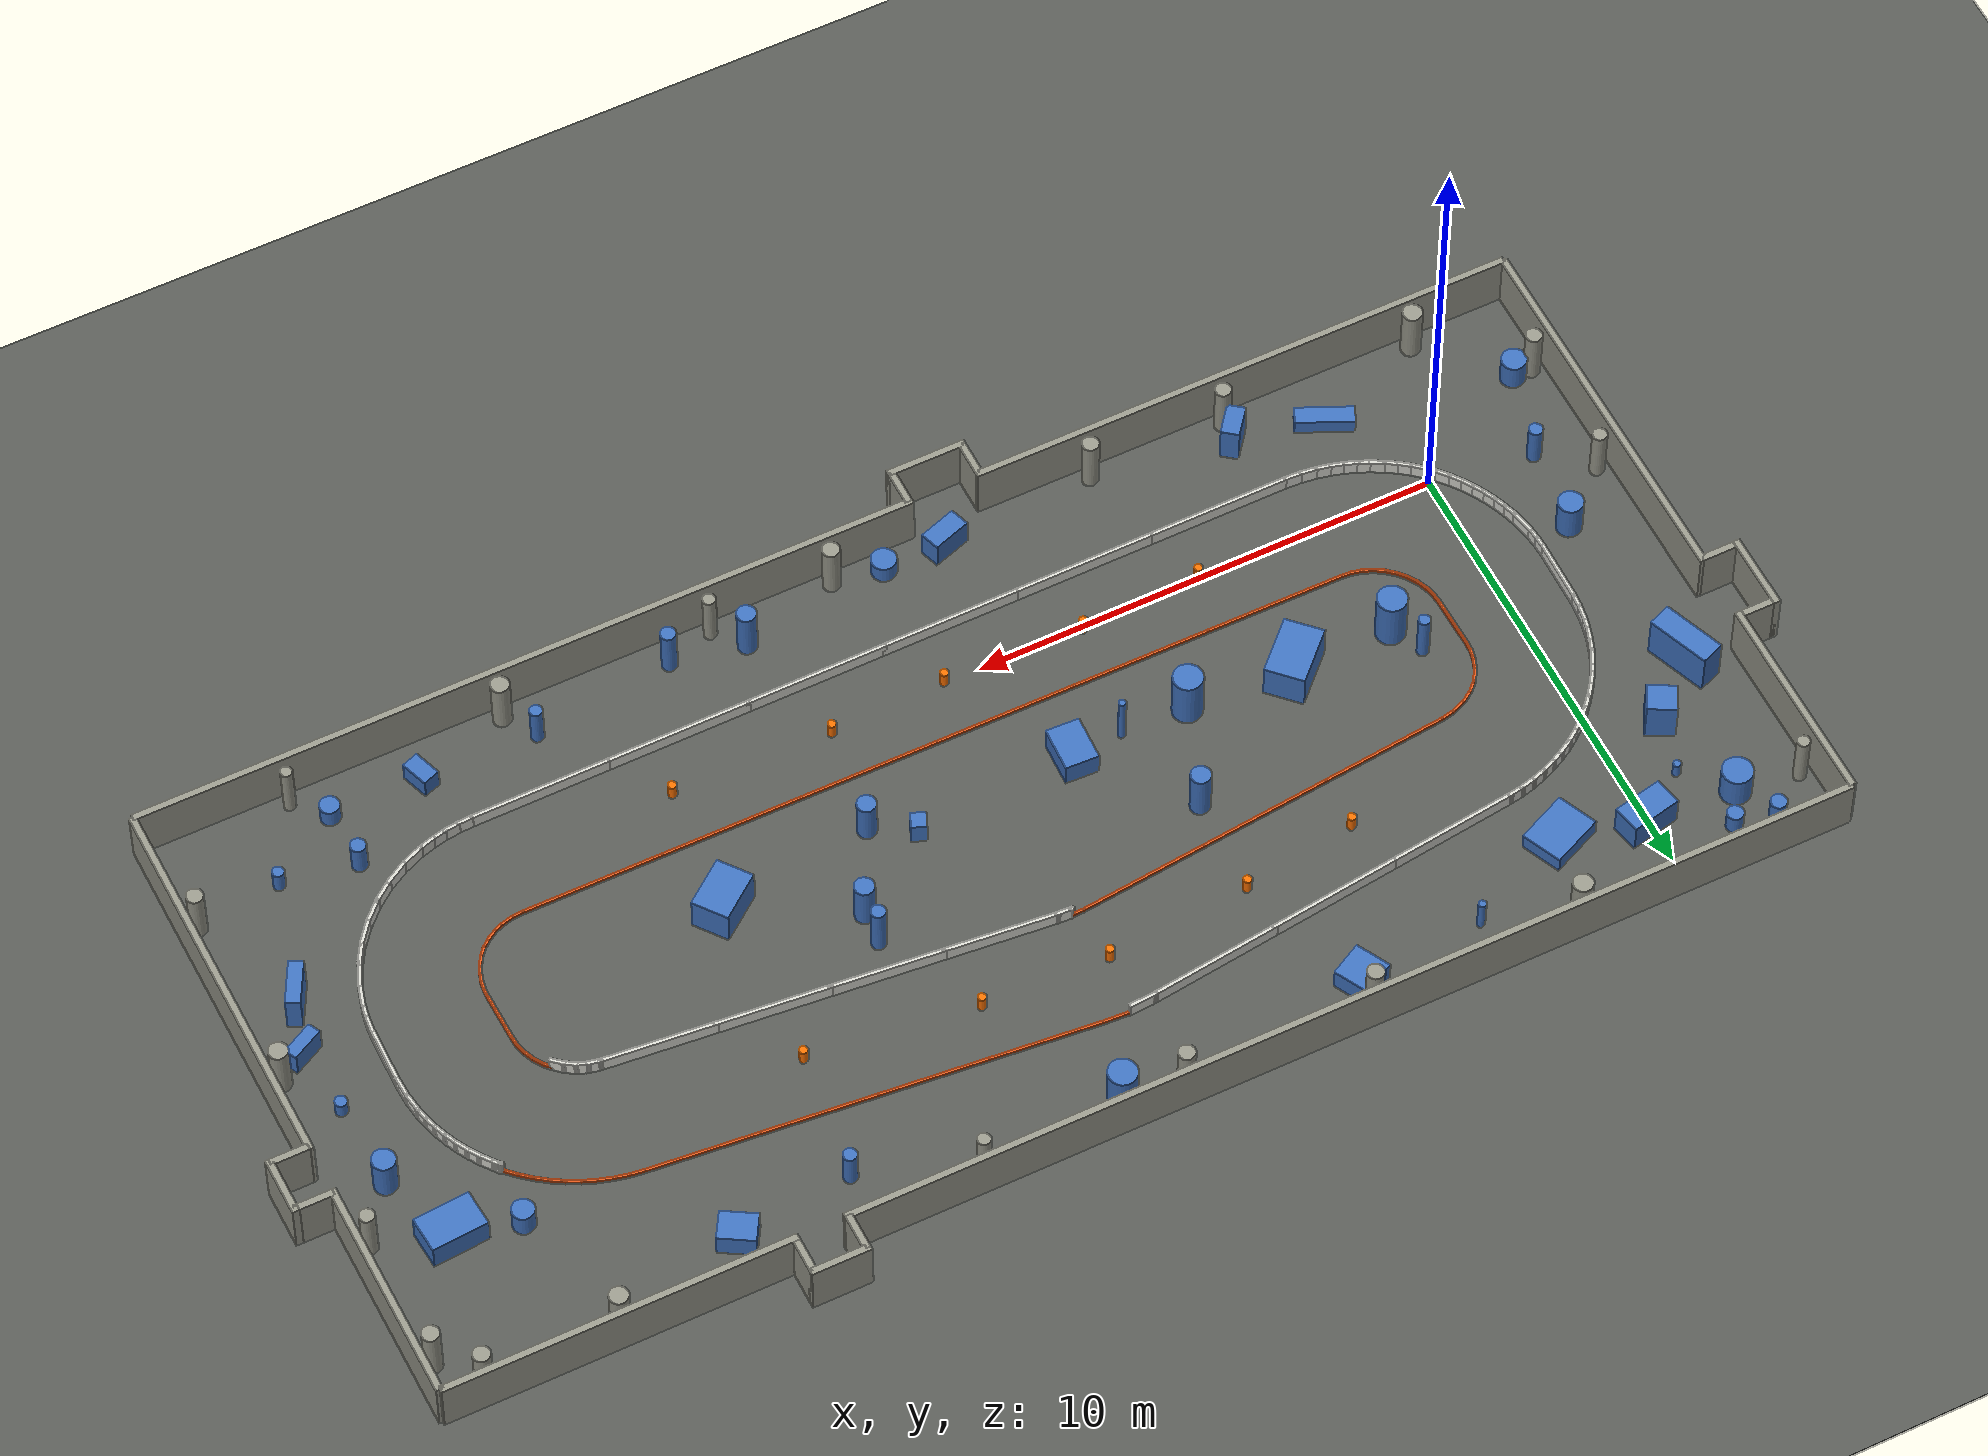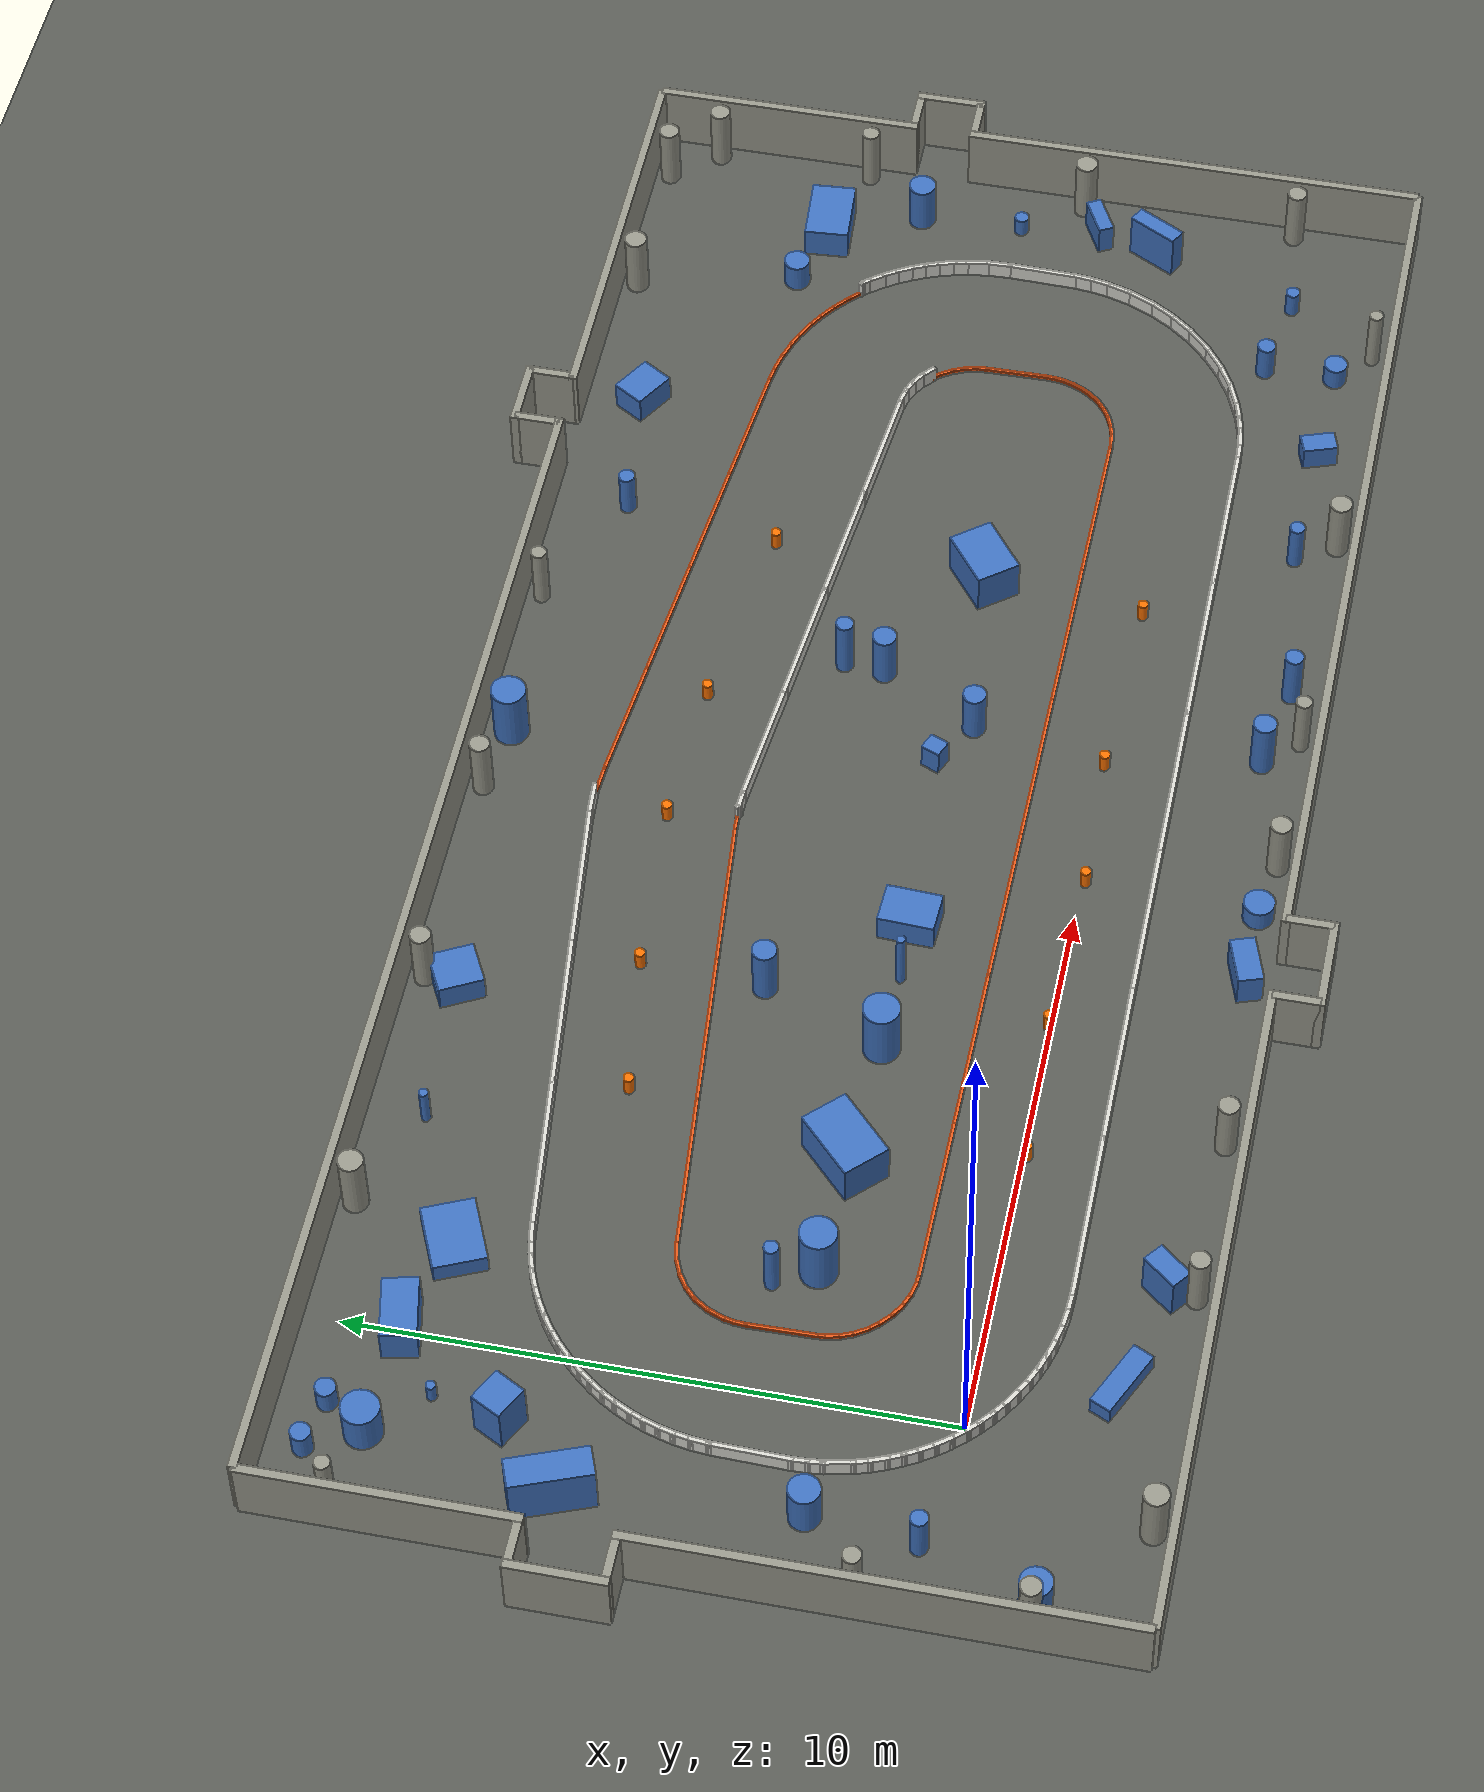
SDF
<?xml version="1.0" ?>
<sdf version="1.9">
  <!-- Generated by simulation/tools/generate_pose_dataset.py --install-gazebo-worlds from tools/pose_dataset/config/tracks.yaml (slalom_cones). Do not edit by hand: change the YAML and regenerate. -->
  <world name="default">
    <physics name="default_physics" type="dart">
      <max_step_size>0.001</max_step_size>
      <real_time_factor>1.0</real_time_factor>
      <real_time_update_rate>1000.0</real_time_update_rate>
    </physics>
    <plugin filename="gz-sim-physics-system" name="gz::sim::systems::Physics" />
    <plugin filename="gz-sim-user-commands-system" name="gz::sim::systems::UserCommands" />
    <plugin filename="gz-sim-scene-broadcaster-system" name="gz::sim::systems::SceneBroadcaster" />
    <plugin filename="gz-sim-imu-system" name="gz::sim::systems::Imu" />
    <plugin filename="gz-sim-sensors-system" name="gz::sim::systems::Sensors">
      <render_engine>ogre2</render_engine>
    </plugin>
    <light type="directional" name="sun">
      <pose>0 0 10 0 0 0</pose>
      <diffuse>0.8 0.8 0.8 1</diffuse>
      <direction>-0.5 0.5 -1</direction>
      <cast_shadows>true</cast_shadows>
    </light>
    <model name="track_curb">
      <static>true</static>
      <pose>0 0 0 0 0 0</pose>
      <link name="curb_link">
        <collision name="left1_0_0_collision">
          <pose>10.853820 5.941970 0.035000 0.000000 0.000000 -3.095750</pose>
          <geometry>
            <box>
              <size>0.336425 0.060000 0.070000</size>
            </box>
          </geometry>
        </collision>
        <visual name="left1_0_0_visual">
          <pose>10.853820 5.941970 0.035000 0.000000 0.000000 -3.095750</pose>
          <geometry>
            <box>
              <size>0.336425 0.060000 0.070000</size>
            </box>
          </geometry>
          <material>
            <ambient>0.9 0.35 0.1 1</ambient>
            <diffuse>0.9 0.35 0.1 1</diffuse>
          </material>
        </visual>
        <collision name="left1_1_0_collision">
          <pose>9.333193 5.797957 0.035000 0.000000 0.000000 -3.042337</pose>
          <geometry>
            <box>
              <size>2.838797 0.060000 0.070000</size>
            </box>
          </geometry>
        </collision>
        <visual name="left1_1_0_visual">
          <pose>9.333193 5.797957 0.035000 0.000000 0.000000 -3.042337</pose>
          <geometry>
            <box>
              <size>2.838797 0.060000 0.070000</size>
            </box>
          </geometry>
          <material>
            <ambient>0.9 0.35 0.1 1</ambient>
            <diffuse>0.9 0.35 0.1 1</diffuse>
          </material>
        </visual>
        <collision name="left1_1_1_collision">
          <pose>6.568073 5.522599 0.035000 0.000000 0.000000 -3.042337</pose>
          <geometry>
            <box>
              <size>2.838797 0.060000 0.070000</size>
            </box>
          </geometry>
        </collision>
        <visual name="left1_1_1_visual">
          <pose>6.568073 5.522599 0.035000 0.000000 0.000000 -3.042337</pose>
          <geometry>
            <box>
              <size>2.838797 0.060000 0.070000</size>
            </box>
          </geometry>
          <material>
            <ambient>0.9 0.35 0.1 1</ambient>
            <diffuse>0.9 0.35 0.1 1</diffuse>
          </material>
        </visual>
        <collision name="left1_1_2_collision">
          <pose>3.802953 5.247240 0.035000 0.000000 0.000000 -3.042337</pose>
          <geometry>
            <box>
              <size>2.838797 0.060000 0.070000</size>
            </box>
          </geometry>
        </collision>
        <visual name="left1_1_2_visual">
          <pose>3.802953 5.247240 0.035000 0.000000 0.000000 -3.042337</pose>
          <geometry>
            <box>
              <size>2.838797 0.060000 0.070000</size>
            </box>
          </geometry>
          <material>
            <ambient>0.9 0.35 0.1 1</ambient>
            <diffuse>0.9 0.35 0.1 1</diffuse>
          </material>
        </visual>
        <collision name="left1_2_0_collision">
          <pose>2.278899 5.079885 0.035000 0.000000 0.000000 -2.934854</pose>
          <geometry>
            <box>
              <size>0.349144 0.060000 0.070000</size>
            </box>
          </geometry>
        </collision>
        <visual name="left1_2_0_visual">
          <pose>2.278899 5.079885 0.035000 0.000000 0.000000 -2.934854</pose>
          <geometry>
            <box>
              <size>0.349144 0.060000 0.070000</size>
            </box>
          </geometry>
          <material>
            <ambient>0.9 0.35 0.1 1</ambient>
            <diffuse>0.9 0.35 0.1 1</diffuse>
          </material>
        </visual>
        <collision name="left1_3_0_collision">
          <pose>2.004133 4.992944 0.035000 0.000000 0.000000 -2.735764</pose>
          <geometry>
            <box>
              <size>0.350111 0.060000 0.070000</size>
            </box>
          </geometry>
        </collision>
        <visual name="left1_3_0_visual">
          <pose>2.004133 4.992944 0.035000 0.000000 0.000000 -2.735764</pose>
          <geometry>
            <box>
              <size>0.350111 0.060000 0.070000</size>
            </box>
          </geometry>
          <material>
            <ambient>0.9 0.35 0.1 1</ambient>
            <diffuse>0.9 0.35 0.1 1</diffuse>
          </material>
        </visual>
        <collision name="left1_4_0_collision">
          <pose>1.759760 4.860119 0.035000 0.000000 0.000000 -2.544340</pose>
          <geometry>
            <box>
              <size>0.328718 0.060000 0.070000</size>
            </box>
          </geometry>
        </collision>
        <visual name="left1_4_0_visual">
          <pose>1.759760 4.860119 0.035000 0.000000 0.000000 -2.544340</pose>
          <geometry>
            <box>
              <size>0.328718 0.060000 0.070000</size>
            </box>
          </geometry>
          <material>
            <ambient>0.9 0.35 0.1 1</ambient>
            <diffuse>0.9 0.35 0.1 1</diffuse>
          </material>
        </visual>
        <collision name="left1_5_0_collision">
          <pose>1.561259 4.697409 0.035000 0.000000 0.000000 -2.357634</pose>
          <geometry>
            <box>
              <size>0.306854 0.060000 0.070000</size>
            </box>
          </geometry>
        </collision>
        <visual name="left1_5_0_visual">
          <pose>1.561259 4.697409 0.035000 0.000000 0.000000 -2.357634</pose>
          <geometry>
            <box>
              <size>0.306854 0.060000 0.070000</size>
            </box>
          </geometry>
          <material>
            <ambient>0.9 0.35 0.1 1</ambient>
            <diffuse>0.9 0.35 0.1 1</diffuse>
          </material>
        </visual>
        <collision name="left1_6_0_collision">
          <pose>1.396379 4.487163 0.035000 0.000000 0.000000 -2.132567</pose>
          <geometry>
            <box>
              <size>0.350898 0.060000 0.070000</size>
            </box>
          </geometry>
        </collision>
        <visual name="left1_6_0_visual">
          <pose>1.396379 4.487163 0.035000 0.000000 0.000000 -2.132567</pose>
          <geometry>
            <box>
              <size>0.350898 0.060000 0.070000</size>
            </box>
          </geometry>
          <material>
            <ambient>0.9 0.35 0.1 1</ambient>
            <diffuse>0.9 0.35 0.1 1</diffuse>
          </material>
        </visual>
        <collision name="left1_7_0_collision">
          <pose>1.267688 4.229029 0.035000 0.000000 0.000000 -1.933281</pose>
          <geometry>
            <box>
              <size>0.348847 0.060000 0.070000</size>
            </box>
          </geometry>
        </collision>
        <visual name="left1_7_0_visual">
          <pose>1.267688 4.229029 0.035000 0.000000 0.000000 -1.933281</pose>
          <geometry>
            <box>
              <size>0.348847 0.060000 0.070000</size>
            </box>
          </geometry>
          <material>
            <ambient>0.9 0.35 0.1 1</ambient>
            <diffuse>0.9 0.35 0.1 1</diffuse>
          </material>
        </visual>
        <collision name="left1_8_0_collision">
          <pose>1.198776 4.007321 0.035000 0.000000 0.000000 -1.772244</pose>
          <geometry>
            <box>
              <size>0.236915 0.060000 0.070000</size>
            </box>
          </geometry>
        </collision>
        <visual name="left1_8_0_visual">
          <pose>1.198776 4.007321 0.035000 0.000000 0.000000 -1.772244</pose>
          <geometry>
            <box>
              <size>0.236915 0.060000 0.070000</size>
            </box>
          </geometry>
          <material>
            <ambient>0.9 0.35 0.1 1</ambient>
            <diffuse>0.9 0.35 0.1 1</diffuse>
          </material>
        </visual>
        <collision name="left1_9_0_collision">
          <pose>1.174069 3.827363 0.035000 0.000000 0.000000 -1.645777</pose>
          <geometry>
            <box>
              <size>0.247105 0.060000 0.070000</size>
            </box>
          </geometry>
        </collision>
        <visual name="left1_9_0_visual">
          <pose>1.174069 3.827363 0.035000 0.000000 0.000000 -1.645777</pose>
          <geometry>
            <box>
              <size>0.247105 0.060000 0.070000</size>
            </box>
          </geometry>
          <material>
            <ambient>0.9 0.35 0.1 1</ambient>
            <diffuse>0.9 0.35 0.1 1</diffuse>
          </material>
        </visual>
        <collision name="left1_10_0_collision">
          <pose>1.178154 3.168180 0.035000 0.000000 0.000000 -1.551197</pose>
          <geometry>
            <box>
              <size>1.192005 0.060000 0.070000</size>
            </box>
          </geometry>
        </collision>
        <visual name="left1_10_0_visual">
          <pose>1.178154 3.168180 0.035000 0.000000 0.000000 -1.551197</pose>
          <geometry>
            <box>
              <size>1.192005 0.060000 0.070000</size>
            </box>
          </geometry>
          <material>
            <ambient>0.9 0.35 0.1 1</ambient>
            <diffuse>0.9 0.35 0.1 1</diffuse>
          </material>
        </visual>
        <collision name="left1_11_0_collision">
          <pose>1.196864 2.520590 0.035000 0.000000 0.000000 -1.477827</pose>
          <geometry>
            <box>
              <size>0.224101 0.060000 0.070000</size>
            </box>
          </geometry>
        </collision>
        <visual name="left1_11_0_visual">
          <pose>1.196864 2.520590 0.035000 0.000000 0.000000 -1.477827</pose>
          <geometry>
            <box>
              <size>0.224101 0.060000 0.070000</size>
            </box>
          </geometry>
          <material>
            <ambient>0.9 0.35 0.1 1</ambient>
            <diffuse>0.9 0.35 0.1 1</diffuse>
          </material>
        </visual>
        <collision name="left1_12_0_collision">
          <pose>1.230417 2.329278 0.035000 0.000000 0.000000 -1.338457</pose>
          <geometry>
            <box>
              <size>0.285285 0.060000 0.070000</size>
            </box>
          </geometry>
        </collision>
        <visual name="left1_12_0_visual">
          <pose>1.230417 2.329278 0.035000 0.000000 0.000000 -1.338457</pose>
          <geometry>
            <box>
              <size>0.285285 0.060000 0.070000</size>
            </box>
          </geometry>
          <material>
            <ambient>0.9 0.35 0.1 1</ambient>
            <diffuse>0.9 0.35 0.1 1</diffuse>
          </material>
        </visual>
        <collision name="left1_13_0_collision">
          <pose>1.299283 2.116248 0.035000 0.000000 0.000000 -1.177324</pose>
          <geometry>
            <box>
              <size>0.283944 0.060000 0.070000</size>
            </box>
          </geometry>
        </collision>
        <visual name="left1_13_0_visual">
          <pose>1.299283 2.116248 0.035000 0.000000 0.000000 -1.177324</pose>
          <geometry>
            <box>
              <size>0.283944 0.060000 0.070000</size>
            </box>
          </geometry>
          <material>
            <ambient>0.9 0.35 0.1 1</ambient>
            <diffuse>0.9 0.35 0.1 1</diffuse>
          </material>
        </visual>
        <collision name="left1_14_0_collision">
          <pose>1.400825 1.918214 0.035000 0.000000 0.000000 -1.016189</pose>
          <geometry>
            <box>
              <size>0.282602 0.060000 0.070000</size>
            </box>
          </geometry>
        </collision>
        <visual name="left1_14_0_visual">
          <pose>1.400825 1.918214 0.035000 0.000000 0.000000 -1.016189</pose>
          <geometry>
            <box>
              <size>0.282602 0.060000 0.070000</size>
            </box>
          </geometry>
          <material>
            <ambient>0.9 0.35 0.1 1</ambient>
            <diffuse>0.9 0.35 0.1 1</diffuse>
          </material>
        </visual>
        <collision name="left1_15_0_collision">
          <pose>1.532031 1.740114 0.035000 0.000000 0.000000 -0.855052</pose>
          <geometry>
            <box>
              <size>0.281261 0.060000 0.070000</size>
            </box>
          </geometry>
        </collision>
        <visual name="left1_15_0_visual">
          <pose>1.532031 1.740114 0.035000 0.000000 0.000000 -0.855052</pose>
          <geometry>
            <box>
              <size>0.281261 0.060000 0.070000</size>
            </box>
          </geometry>
          <material>
            <ambient>0.9 0.35 0.1 1</ambient>
            <diffuse>0.9 0.35 0.1 1</diffuse>
          </material>
        </visual>
        <collision name="left1_16_0_collision">
          <pose>1.694918 1.576526 0.035000 0.000000 0.000000 -0.725679</pose>
          <geometry>
            <box>
              <size>0.301410 0.060000 0.070000</size>
            </box>
          </geometry>
        </collision>
        <visual name="left1_16_0_visual">
          <pose>1.694918 1.576526 0.035000 0.000000 0.000000 -0.725679</pose>
          <geometry>
            <box>
              <size>0.301410 0.060000 0.070000</size>
            </box>
          </geometry>
          <material>
            <ambient>0.9 0.35 0.1 1</ambient>
            <diffuse>0.9 0.35 0.1 1</diffuse>
          </material>
        </visual>
        <collision name="left1_17_0_collision">
          <pose>1.883112 1.434998 0.035000 0.000000 0.000000 -0.560328</pose>
          <geometry>
            <box>
              <size>0.291148 0.060000 0.070000</size>
            </box>
          </geometry>
        </collision>
        <visual name="left1_17_0_visual">
          <pose>1.883112 1.434998 0.035000 0.000000 0.000000 -0.560328</pose>
          <geometry>
            <box>
              <size>0.291148 0.060000 0.070000</size>
            </box>
          </geometry>
          <material>
            <ambient>0.9 0.35 0.1 1</ambient>
            <diffuse>0.9 0.35 0.1 1</diffuse>
          </material>
        </visual>
        <collision name="left1_18_0_collision">
          <pose>2.093017 1.327808 0.035000 0.000000 0.000000 -0.387909</pose>
          <geometry>
            <box>
              <size>0.301989 0.060000 0.070000</size>
            </box>
          </geometry>
        </collision>
        <visual name="left1_18_0_visual">
          <pose>2.093017 1.327808 0.035000 0.000000 0.000000 -0.387909</pose>
          <geometry>
            <box>
              <size>0.301989 0.060000 0.070000</size>
            </box>
          </geometry>
          <material>
            <ambient>0.9 0.35 0.1 1</ambient>
            <diffuse>0.9 0.35 0.1 1</diffuse>
          </material>
        </visual>
        <collision name="left1_19_0_collision">
          <pose>2.318259 1.257255 0.035000 0.000000 0.000000 -0.215494</pose>
          <geometry>
            <box>
              <size>0.291838 0.060000 0.070000</size>
            </box>
          </geometry>
        </collision>
        <visual name="left1_19_0_visual">
          <pose>2.318259 1.257255 0.035000 0.000000 0.000000 -0.215494</pose>
          <geometry>
            <box>
              <size>0.291838 0.060000 0.070000</size>
            </box>
          </geometry>
          <material>
            <ambient>0.9 0.35 0.1 1</ambient>
            <diffuse>0.9 0.35 0.1 1</diffuse>
          </material>
        </visual>
        <collision name="left1_20_0_collision">
          <pose>2.516915 1.226567 0.035000 0.000000 0.000000 -0.068967</pose>
          <geometry>
            <box>
              <size>0.231244 0.060000 0.070000</size>
            </box>
          </geometry>
        </collision>
        <visual name="left1_20_0_visual">
          <pose>2.516915 1.226567 0.035000 0.000000 0.000000 -0.068967</pose>
          <geometry>
            <box>
              <size>0.231244 0.060000 0.070000</size>
            </box>
          </geometry>
          <material>
            <ambient>0.9 0.35 0.1 1</ambient>
            <diffuse>0.9 0.35 0.1 1</diffuse>
          </material>
        </visual>
        <collision name="left1_21_0_collision">
          <pose>4.085291 1.213889 0.035000 0.000000 0.000000 -0.004571</pose>
          <geometry>
            <box>
              <size>3.025946 0.060000 0.070000</size>
            </box>
          </geometry>
        </collision>
        <visual name="left1_21_0_visual">
          <pose>4.085291 1.213889 0.035000 0.000000 0.000000 -0.004571</pose>
          <geometry>
            <box>
              <size>3.025946 0.060000 0.070000</size>
            </box>
          </geometry>
          <material>
            <ambient>0.9 0.35 0.1 1</ambient>
            <diffuse>0.9 0.35 0.1 1</diffuse>
          </material>
        </visual>
        <collision name="left1_21_1_collision">
          <pose>7.051206 1.200332 0.035000 0.000000 0.000000 -0.004571</pose>
          <geometry>
            <box>
              <size>3.025946 0.060000 0.070000</size>
            </box>
          </geometry>
        </collision>
        <visual name="left1_21_1_visual">
          <pose>7.051206 1.200332 0.035000 0.000000 0.000000 -0.004571</pose>
          <geometry>
            <box>
              <size>3.025946 0.060000 0.070000</size>
            </box>
          </geometry>
          <material>
            <ambient>0.9 0.35 0.1 1</ambient>
            <diffuse>0.9 0.35 0.1 1</diffuse>
          </material>
        </visual>
        <collision name="left1_21_2_collision">
          <pose>10.017120 1.186776 0.035000 0.000000 0.000000 -0.004571</pose>
          <geometry>
            <box>
              <size>3.025946 0.060000 0.070000</size>
            </box>
          </geometry>
        </collision>
        <visual name="left1_21_2_visual">
          <pose>10.017120 1.186776 0.035000 0.000000 0.000000 -0.004571</pose>
          <geometry>
            <box>
              <size>3.025946 0.060000 0.070000</size>
            </box>
          </geometry>
          <material>
            <ambient>0.9 0.35 0.1 1</ambient>
            <diffuse>0.9 0.35 0.1 1</diffuse>
          </material>
        </visual>
        <collision name="left1_21_3_collision">
          <pose>12.983035 1.173220 0.035000 0.000000 0.000000 -0.004571</pose>
          <geometry>
            <box>
              <size>3.025946 0.060000 0.070000</size>
            </box>
          </geometry>
        </collision>
        <visual name="left1_21_3_visual">
          <pose>12.983035 1.173220 0.035000 0.000000 0.000000 -0.004571</pose>
          <geometry>
            <box>
              <size>3.025946 0.060000 0.070000</size>
            </box>
          </geometry>
          <material>
            <ambient>0.9 0.35 0.1 1</ambient>
            <diffuse>0.9 0.35 0.1 1</diffuse>
          </material>
        </visual>
        <collision name="left1_21_4_collision">
          <pose>15.948950 1.159664 0.035000 0.000000 0.000000 -0.004571</pose>
          <geometry>
            <box>
              <size>3.025946 0.060000 0.070000</size>
            </box>
          </geometry>
        </collision>
        <visual name="left1_21_4_visual">
          <pose>15.948950 1.159664 0.035000 0.000000 0.000000 -0.004571</pose>
          <geometry>
            <box>
              <size>3.025946 0.060000 0.070000</size>
            </box>
          </geometry>
          <material>
            <ambient>0.9 0.35 0.1 1</ambient>
            <diffuse>0.9 0.35 0.1 1</diffuse>
          </material>
        </visual>
        <collision name="left1_21_5_collision">
          <pose>18.914864 1.146107 0.035000 0.000000 0.000000 -0.004571</pose>
          <geometry>
            <box>
              <size>3.025946 0.060000 0.070000</size>
            </box>
          </geometry>
        </collision>
        <visual name="left1_21_5_visual">
          <pose>18.914864 1.146107 0.035000 0.000000 0.000000 -0.004571</pose>
          <geometry>
            <box>
              <size>3.025946 0.060000 0.070000</size>
            </box>
          </geometry>
          <material>
            <ambient>0.9 0.35 0.1 1</ambient>
            <diffuse>0.9 0.35 0.1 1</diffuse>
          </material>
        </visual>
        <collision name="left1_22_0_collision">
          <pose>20.532662 1.150571 0.035000 0.000000 0.000000 0.083178</pose>
          <geometry>
            <box>
              <size>0.330616 0.060000 0.070000</size>
            </box>
          </geometry>
        </collision>
        <visual name="left1_22_0_visual">
          <pose>20.532662 1.150571 0.035000 0.000000 0.000000 0.083178</pose>
          <geometry>
            <box>
              <size>0.330616 0.060000 0.070000</size>
            </box>
          </geometry>
          <material>
            <ambient>0.9 0.35 0.1 1</ambient>
            <diffuse>0.9 0.35 0.1 1</diffuse>
          </material>
        </visual>
        <collision name="left1_23_0_collision">
          <pose>20.776005 1.189798 0.035000 0.000000 0.000000 0.252422</pose>
          <geometry>
            <box>
              <size>0.284107 0.060000 0.070000</size>
            </box>
          </geometry>
        </collision>
        <visual name="left1_23_0_visual">
          <pose>20.776005 1.189798 0.035000 0.000000 0.000000 0.252422</pose>
          <geometry>
            <box>
              <size>0.284107 0.060000 0.070000</size>
            </box>
          </geometry>
          <material>
            <ambient>0.9 0.35 0.1 1</ambient>
            <diffuse>0.9 0.35 0.1 1</diffuse>
          </material>
        </visual>
        <collision name="left1_24_0_collision">
          <pose>20.982607 1.259473 0.035000 0.000000 0.000000 0.401847</pose>
          <geometry>
            <box>
              <size>0.273181 0.060000 0.070000</size>
            </box>
          </geometry>
        </collision>
        <visual name="left1_24_0_visual">
          <pose>20.982607 1.259473 0.035000 0.000000 0.000000 0.401847</pose>
          <geometry>
            <box>
              <size>0.273181 0.060000 0.070000</size>
            </box>
          </geometry>
          <material>
            <ambient>0.9 0.35 0.1 1</ambient>
            <diffuse>0.9 0.35 0.1 1</diffuse>
          </material>
        </visual>
        <collision name="left1_25_0_collision">
          <pose>21.171827 1.356709 0.035000 0.000000 0.000000 0.547443</pose>
          <geometry>
            <box>
              <size>0.273432 0.060000 0.070000</size>
            </box>
          </geometry>
        </collision>
        <visual name="left1_25_0_visual">
          <pose>21.171827 1.356709 0.035000 0.000000 0.000000 0.547443</pose>
          <geometry>
            <box>
              <size>0.273432 0.060000 0.070000</size>
            </box>
          </geometry>
          <material>
            <ambient>0.9 0.35 0.1 1</ambient>
            <diffuse>0.9 0.35 0.1 1</diffuse>
          </material>
        </visual>
        <collision name="left1_26_0_collision">
          <pose>21.345142 1.480514 0.035000 0.000000 0.000000 0.693038</pose>
          <geometry>
            <box>
              <size>0.273684 0.060000 0.070000</size>
            </box>
          </geometry>
        </collision>
        <visual name="left1_26_0_visual">
          <pose>21.345142 1.480514 0.035000 0.000000 0.000000 0.693038</pose>
          <geometry>
            <box>
              <size>0.273684 0.060000 0.070000</size>
            </box>
          </geometry>
          <material>
            <ambient>0.9 0.35 0.1 1</ambient>
            <diffuse>0.9 0.35 0.1 1</diffuse>
          </material>
        </visual>
        <collision name="left1_27_0_collision">
          <pose>21.492179 1.626357 0.035000 0.000000 0.000000 0.874620</pose>
          <geometry>
            <box>
              <size>0.262227 0.060000 0.070000</size>
            </box>
          </geometry>
        </collision>
        <visual name="left1_27_0_visual">
          <pose>21.492179 1.626357 0.035000 0.000000 0.000000 0.874620</pose>
          <geometry>
            <box>
              <size>0.262227 0.060000 0.070000</size>
            </box>
          </geometry>
          <material>
            <ambient>0.9 0.35 0.1 1</ambient>
            <diffuse>0.9 0.35 0.1 1</diffuse>
          </material>
        </visual>
        <collision name="left1_28_0_collision">
          <pose>21.610017 1.789518 0.035000 0.000000 0.000000 1.016328</pose>
          <geometry>
            <box>
              <size>0.261314 0.060000 0.070000</size>
            </box>
          </geometry>
        </collision>
        <visual name="left1_28_0_visual">
          <pose>21.610017 1.789518 0.035000 0.000000 0.000000 1.016328</pose>
          <geometry>
            <box>
              <size>0.261314 0.060000 0.070000</size>
            </box>
          </geometry>
          <material>
            <ambient>0.9 0.35 0.1 1</ambient>
            <diffuse>0.9 0.35 0.1 1</diffuse>
          </material>
        </visual>
        <collision name="left1_29_0_collision">
          <pose>21.703522 1.966700 0.035000 0.000000 0.000000 1.154427</pose>
          <geometry>
            <box>
              <size>0.260327 0.060000 0.070000</size>
            </box>
          </geometry>
        </collision>
        <visual name="left1_29_0_visual">
          <pose>21.703522 1.966700 0.035000 0.000000 0.000000 1.154427</pose>
          <geometry>
            <box>
              <size>0.260327 0.060000 0.070000</size>
            </box>
          </geometry>
          <material>
            <ambient>0.9 0.35 0.1 1</ambient>
            <diffuse>0.9 0.35 0.1 1</diffuse>
          </material>
        </visual>
        <collision name="left1_30_0_collision">
          <pose>21.771411 2.154142 0.035000 0.000000 0.000000 1.292527</pose>
          <geometry>
            <box>
              <size>0.259339 0.060000 0.070000</size>
            </box>
          </geometry>
        </collision>
        <visual name="left1_30_0_visual">
          <pose>21.771411 2.154142 0.035000 0.000000 0.000000 1.292527</pose>
          <geometry>
            <box>
              <size>0.259339 0.060000 0.070000</size>
            </box>
          </geometry>
          <material>
            <ambient>0.9 0.35 0.1 1</ambient>
            <diffuse>0.9 0.35 0.1 1</diffuse>
          </material>
        </visual>
        <collision name="left1_31_0_collision">
          <pose>21.810746 2.326250 0.035000 0.000000 0.000000 1.415307</pose>
          <geometry>
            <box>
              <size>0.214408 0.060000 0.070000</size>
            </box>
          </geometry>
        </collision>
        <visual name="left1_31_0_visual">
          <pose>21.810746 2.326250 0.035000 0.000000 0.000000 1.415307</pose>
          <geometry>
            <box>
              <size>0.214408 0.060000 0.070000</size>
            </box>
          </geometry>
          <material>
            <ambient>0.9 0.35 0.1 1</ambient>
            <diffuse>0.9 0.35 0.1 1</diffuse>
          </material>
        </visual>
        <collision name="left1_32_0_collision">
          <pose>21.826398 2.479338 0.035000 0.000000 0.000000 1.522721</pose>
          <geometry>
            <box>
              <size>0.213810 0.060000 0.070000</size>
            </box>
          </geometry>
        </collision>
        <visual name="left1_32_0_visual">
          <pose>21.826398 2.479338 0.035000 0.000000 0.000000 1.522721</pose>
          <geometry>
            <box>
              <size>0.213810 0.060000 0.070000</size>
            </box>
          </geometry>
          <material>
            <ambient>0.9 0.35 0.1 1</ambient>
            <diffuse>0.9 0.35 0.1 1</diffuse>
          </material>
        </visual>
        <collision name="left1_33_0_collision">
          <pose>21.819167 3.100447 0.035000 0.000000 0.000000 1.590869</pose>
          <geometry>
            <box>
              <size>1.148805 0.060000 0.070000</size>
            </box>
          </geometry>
        </collision>
        <visual name="left1_33_0_visual">
          <pose>21.819167 3.100447 0.035000 0.000000 0.000000 1.590869</pose>
          <geometry>
            <box>
              <size>1.148805 0.060000 0.070000</size>
            </box>
          </geometry>
          <material>
            <ambient>0.9 0.35 0.1 1</ambient>
            <diffuse>0.9 0.35 0.1 1</diffuse>
          </material>
        </visual>
        <collision name="left1_34_0_collision">
          <pose>21.798917 3.736903 0.035000 0.000000 0.000000 1.671610</pose>
          <geometry>
            <box>
              <size>0.245267 0.060000 0.070000</size>
            </box>
          </geometry>
        </collision>
        <visual name="left1_34_0_visual">
          <pose>21.798917 3.736903 0.035000 0.000000 0.000000 1.671610</pose>
          <geometry>
            <box>
              <size>0.245267 0.060000 0.070000</size>
            </box>
          </geometry>
          <material>
            <ambient>0.9 0.35 0.1 1</ambient>
            <diffuse>0.9 0.35 0.1 1</diffuse>
          </material>
        </visual>
        <collision name="left1_35_0_collision">
          <pose>21.763735 3.932942 0.035000 0.000000 0.000000 1.814782</pose>
          <geometry>
            <box>
              <size>0.274092 0.060000 0.070000</size>
            </box>
          </geometry>
        </collision>
        <visual name="left1_35_0_visual">
          <pose>21.763735 3.932942 0.035000 0.000000 0.000000 1.814782</pose>
          <geometry>
            <box>
              <size>0.274092 0.060000 0.070000</size>
            </box>
          </geometry>
          <material>
            <ambient>0.9 0.35 0.1 1</ambient>
            <diffuse>0.9 0.35 0.1 1</diffuse>
          </material>
        </visual>
        <collision name="left1_36_0_collision">
          <pose>21.694235 4.139673 0.035000 0.000000 0.000000 1.972066</pose>
          <geometry>
            <box>
              <size>0.283462 0.060000 0.070000</size>
            </box>
          </geometry>
        </collision>
        <visual name="left1_36_0_visual">
          <pose>21.694235 4.139673 0.035000 0.000000 0.000000 1.972066</pose>
          <geometry>
            <box>
              <size>0.283462 0.060000 0.070000</size>
            </box>
          </geometry>
          <material>
            <ambient>0.9 0.35 0.1 1</ambient>
            <diffuse>0.9 0.35 0.1 1</diffuse>
          </material>
        </visual>
        <collision name="left1_37_0_collision">
          <pose>21.584982 4.344879 0.035000 0.000000 0.000000 2.140853</pose>
          <geometry>
            <box>
              <size>0.303150 0.060000 0.070000</size>
            </box>
          </geometry>
        </collision>
        <visual name="left1_37_0_visual">
          <pose>21.584982 4.344879 0.035000 0.000000 0.000000 2.140853</pose>
          <geometry>
            <box>
              <size>0.303150 0.060000 0.070000</size>
            </box>
          </geometry>
          <material>
            <ambient>0.9 0.35 0.1 1</ambient>
            <diffuse>0.9 0.35 0.1 1</diffuse>
          </material>
        </visual>
        <collision name="left1_38_0_collision">
          <pose>21.467581 4.506770 0.035000 0.000000 0.000000 2.286696</pose>
          <geometry>
            <box>
              <size>0.217826 0.060000 0.070000</size>
            </box>
          </geometry>
        </collision>
        <visual name="left1_38_0_visual">
          <pose>21.467581 4.506770 0.035000 0.000000 0.000000 2.286696</pose>
          <geometry>
            <box>
              <size>0.217826 0.060000 0.070000</size>
            </box>
          </geometry>
          <material>
            <ambient>0.9 0.35 0.1 1</ambient>
            <diffuse>0.9 0.35 0.1 1</diffuse>
          </material>
        </visual>
        <collision name="left1_39_0_collision">
          <pose>21.408572 4.566804 0.035000 0.000000 0.000000 3.073180</pose>
          <geometry>
            <box>
              <size>0.074470 0.060000 0.070000</size>
            </box>
          </geometry>
        </collision>
        <visual name="left1_39_0_visual">
          <pose>21.408572 4.566804 0.035000 0.000000 0.000000 3.073180</pose>
          <geometry>
            <box>
              <size>0.074470 0.060000 0.070000</size>
            </box>
          </geometry>
          <material>
            <ambient>0.9 0.35 0.1 1</ambient>
            <diffuse>0.9 0.35 0.1 1</diffuse>
          </material>
        </visual>
        <collision name="right0_0_0_collision">
          <pose>23.116662 6.342794 0.035000 0.000000 0.000000 2.352333</pose>
          <geometry>
            <box>
              <size>0.353388 0.060000 0.070000</size>
            </box>
          </geometry>
        </collision>
        <visual name="right0_0_0_visual">
          <pose>23.116662 6.342794 0.035000 0.000000 0.000000 2.352333</pose>
          <geometry>
            <box>
              <size>0.353388 0.060000 0.070000</size>
            </box>
          </geometry>
          <material>
            <ambient>0.9 0.35 0.1 1</ambient>
            <diffuse>0.9 0.35 0.1 1</diffuse>
          </material>
        </visual>
        <collision name="right0_1_0_collision">
          <pose>22.890844 6.551952 0.035000 0.000000 0.000000 2.432785</pose>
          <geometry>
            <box>
              <size>0.382710 0.060000 0.070000</size>
            </box>
          </geometry>
        </collision>
        <visual name="right0_1_0_visual">
          <pose>22.890844 6.551952 0.035000 0.000000 0.000000 2.432785</pose>
          <geometry>
            <box>
              <size>0.382710 0.060000 0.070000</size>
            </box>
          </geometry>
          <material>
            <ambient>0.9 0.35 0.1 1</ambient>
            <diffuse>0.9 0.35 0.1 1</diffuse>
          </material>
        </visual>
        <collision name="right0_2_0_collision">
          <pose>22.637456 6.751329 0.035000 0.000000 0.000000 2.517069</pose>
          <geometry>
            <box>
              <size>0.382710 0.060000 0.070000</size>
            </box>
          </geometry>
        </collision>
        <visual name="right0_2_0_visual">
          <pose>22.637456 6.751329 0.035000 0.000000 0.000000 2.517069</pose>
          <geometry>
            <box>
              <size>0.382710 0.060000 0.070000</size>
            </box>
          </geometry>
          <material>
            <ambient>0.9 0.35 0.1 1</ambient>
            <diffuse>0.9 0.35 0.1 1</diffuse>
          </material>
        </visual>
        <collision name="right0_3_0_collision">
          <pose>22.381046 6.921607 0.035000 0.000000 0.000000 2.597521</pose>
          <geometry>
            <box>
              <size>0.353388 0.060000 0.070000</size>
            </box>
          </geometry>
        </collision>
        <visual name="right0_3_0_visual">
          <pose>22.381046 6.921607 0.035000 0.000000 0.000000 2.597521</pose>
          <geometry>
            <box>
              <size>0.353388 0.060000 0.070000</size>
            </box>
          </geometry>
          <material>
            <ambient>0.9 0.35 0.1 1</ambient>
            <diffuse>0.9 0.35 0.1 1</diffuse>
          </material>
        </visual>
        <collision name="right0_4_0_collision">
          <pose>22.111211 7.069695 0.035000 0.000000 0.000000 2.677973</pose>
          <geometry>
            <box>
              <size>0.382710 0.060000 0.070000</size>
            </box>
          </geometry>
        </collision>
        <visual name="right0_4_0_visual">
          <pose>22.111211 7.069695 0.035000 0.000000 0.000000 2.677973</pose>
          <geometry>
            <box>
              <size>0.382710 0.060000 0.070000</size>
            </box>
          </geometry>
          <material>
            <ambient>0.9 0.35 0.1 1</ambient>
            <diffuse>0.9 0.35 0.1 1</diffuse>
          </material>
        </visual>
        <collision name="right0_5_0_collision">
          <pose>21.830833 7.196694 0.035000 0.000000 0.000000 2.758425</pose>
          <geometry>
            <box>
              <size>0.353388 0.060000 0.070000</size>
            </box>
          </geometry>
        </collision>
        <visual name="right0_5_0_visual">
          <pose>21.830833 7.196694 0.035000 0.000000 0.000000 2.758425</pose>
          <geometry>
            <box>
              <size>0.353388 0.060000 0.070000</size>
            </box>
          </geometry>
          <material>
            <ambient>0.9 0.35 0.1 1</ambient>
            <diffuse>0.9 0.35 0.1 1</diffuse>
          </material>
        </visual>
        <collision name="right0_6_0_collision">
          <pose>21.540758 7.299639 0.035000 0.000000 0.000000 2.838878</pose>
          <geometry>
            <box>
              <size>0.382710 0.060000 0.070000</size>
            </box>
          </geometry>
        </collision>
        <visual name="right0_6_0_visual">
          <pose>21.540758 7.299639 0.035000 0.000000 0.000000 2.838878</pose>
          <geometry>
            <box>
              <size>0.382710 0.060000 0.070000</size>
            </box>
          </geometry>
          <material>
            <ambient>0.9 0.35 0.1 1</ambient>
            <diffuse>0.9 0.35 0.1 1</diffuse>
          </material>
        </visual>
        <collision name="right0_7_0_collision">
          <pose>21.229219 7.382706 0.035000 0.000000 0.000000 2.923161</pose>
          <geometry>
            <box>
              <size>0.382710 0.060000 0.070000</size>
            </box>
          </geometry>
        </collision>
        <visual name="right0_7_0_visual">
          <pose>21.229219 7.382706 0.035000 0.000000 0.000000 2.923161</pose>
          <geometry>
            <box>
              <size>0.382710 0.060000 0.070000</size>
            </box>
          </geometry>
          <material>
            <ambient>0.9 0.35 0.1 1</ambient>
            <diffuse>0.9 0.35 0.1 1</diffuse>
          </material>
        </visual>
        <collision name="right0_8_0_collision">
          <pose>20.927569 7.437730 0.035000 0.000000 0.000000 3.003311</pose>
          <geometry>
            <box>
              <size>0.351036 0.060000 0.070000</size>
            </box>
          </geometry>
        </collision>
        <visual name="right0_8_0_visual">
          <pose>20.927569 7.437730 0.035000 0.000000 0.000000 3.003311</pose>
          <geometry>
            <box>
              <size>0.351036 0.060000 0.070000</size>
            </box>
          </geometry>
          <material>
            <ambient>0.9 0.35 0.1 1</ambient>
            <diffuse>0.9 0.35 0.1 1</diffuse>
          </material>
        </visual>
        <collision name="right0_9_0_collision">
          <pose>19.627632 7.573369 0.035000 0.000000 0.000000 3.041924</pose>
          <geometry>
            <box>
              <size>2.383146 0.060000 0.070000</size>
            </box>
          </geometry>
        </collision>
        <visual name="right0_9_0_visual">
          <pose>19.627632 7.573369 0.035000 0.000000 0.000000 3.041924</pose>
          <geometry>
            <box>
              <size>2.383146 0.060000 0.070000</size>
            </box>
          </geometry>
          <material>
            <ambient>0.9 0.35 0.1 1</ambient>
            <diffuse>0.9 0.35 0.1 1</diffuse>
          </material>
        </visual>
        <collision name="right0_9_1_collision">
          <pose>17.316016 7.804531 0.035000 0.000000 0.000000 3.041924</pose>
          <geometry>
            <box>
              <size>2.383146 0.060000 0.070000</size>
            </box>
          </geometry>
        </collision>
        <visual name="right0_9_1_visual">
          <pose>17.316016 7.804531 0.035000 0.000000 0.000000 3.041924</pose>
          <geometry>
            <box>
              <size>2.383146 0.060000 0.070000</size>
            </box>
          </geometry>
          <material>
            <ambient>0.9 0.35 0.1 1</ambient>
            <diffuse>0.9 0.35 0.1 1</diffuse>
          </material>
        </visual>
        <collision name="right0_9_2_collision">
          <pose>15.004399 8.035693 0.035000 0.000000 0.000000 3.041924</pose>
          <geometry>
            <box>
              <size>2.383146 0.060000 0.070000</size>
            </box>
          </geometry>
        </collision>
        <visual name="right0_9_2_visual">
          <pose>15.004399 8.035693 0.035000 0.000000 0.000000 3.041924</pose>
          <geometry>
            <box>
              <size>2.383146 0.060000 0.070000</size>
            </box>
          </geometry>
          <material>
            <ambient>0.9 0.35 0.1 1</ambient>
            <diffuse>0.9 0.35 0.1 1</diffuse>
          </material>
        </visual>
        <collision name="right0_9_3_collision">
          <pose>12.692783 8.266855 0.035000 0.000000 0.000000 3.041924</pose>
          <geometry>
            <box>
              <size>2.383146 0.060000 0.070000</size>
            </box>
          </geometry>
        </collision>
        <visual name="right0_9_3_visual">
          <pose>12.692783 8.266855 0.035000 0.000000 0.000000 3.041924</pose>
          <geometry>
            <box>
              <size>2.383146 0.060000 0.070000</size>
            </box>
          </geometry>
          <material>
            <ambient>0.9 0.35 0.1 1</ambient>
            <diffuse>0.9 0.35 0.1 1</diffuse>
          </material>
        </visual>
        <collision name="right0_10_0_collision">
          <pose>11.252754 8.400129 0.035000 0.000000 0.000000 3.079425</pose>
          <geometry>
            <box>
              <size>0.629542 0.060000 0.070000</size>
            </box>
          </geometry>
        </collision>
        <visual name="right0_10_0_visual">
          <pose>11.252754 8.400129 0.035000 0.000000 0.000000 3.079425</pose>
          <geometry>
            <box>
              <size>0.629542 0.060000 0.070000</size>
            </box>
          </geometry>
          <material>
            <ambient>0.9 0.35 0.1 1</ambient>
            <diffuse>0.9 0.35 0.1 1</diffuse>
          </material>
        </visual>
      </link>
    </model>
    <model name="track_feature">
      <static>true</static>
      <pose>0 0 0 0 0 0</pose>
      <link name="feature_link">
        <collision name="feat_box_1_collision">
          <pose>24.670382 7.119994 0.289913 0.000000 0.000000 0.071686</pose>
          <geometry>
            <box>
              <size>1.201036 0.794350 0.579826</size>
            </box>
          </geometry>
        </collision>
        <visual name="feat_box_1_visual">
          <pose>24.670382 7.119994 0.289913 0.000000 0.000000 0.071686</pose>
          <geometry>
            <box>
              <size>1.201036 0.794350 0.579826</size>
            </box>
          </geometry>
          <material>
            <ambient>0.25 0.45 0.75 1</ambient>
            <diffuse>0.25 0.45 0.75 1</diffuse>
          </material>
        </visual>
        <collision name="feat_box_3_collision">
          <pose>-1.304008 7.081642 0.461759 0.000000 0.000000 -2.052050</pose>
          <geometry>
            <box>
              <size>0.569174 0.608548 0.923518</size>
            </box>
          </geometry>
        </collision>
        <visual name="feat_box_3_visual">
          <pose>-1.304008 7.081642 0.461759 0.000000 0.000000 -2.052050</pose>
          <geometry>
            <box>
              <size>0.569174 0.608548 0.923518</size>
            </box>
          </geometry>
          <material>
            <ambient>0.25 0.45 0.75 1</ambient>
            <diffuse>0.25 0.45 0.75 1</diffuse>
          </material>
        </visual>
        <collision name="feat_box_4_collision">
          <pose>1.746492 8.575024 0.182613 0.000000 0.000000 0.418718</pose>
          <geometry>
            <box>
              <size>1.158032 0.896006 0.365227</size>
            </box>
          </geometry>
        </collision>
        <visual name="feat_box_4_visual">
          <pose>1.746492 8.575024 0.182613 0.000000 0.000000 0.418718</pose>
          <geometry>
            <box>
              <size>1.158032 0.896006 0.365227</size>
            </box>
          </geometry>
          <material>
            <ambient>0.25 0.45 0.75 1</ambient>
            <diffuse>0.25 0.45 0.75 1</diffuse>
          </material>
        </visual>
        <collision name="feat_box_8_collision">
          <pose>19.882940 9.591676 0.262900 0.000000 0.000000 -0.544129</pose>
          <geometry>
            <box>
              <size>0.775148 0.607738 0.525799</size>
            </box>
          </geometry>
        </collision>
        <visual name="feat_box_8_visual">
          <pose>19.882940 9.591676 0.262900 0.000000 0.000000 -0.544129</pose>
          <geometry>
            <box>
              <size>0.775148 0.607738 0.525799</size>
            </box>
          </geometry>
          <material>
            <ambient>0.25 0.45 0.75 1</ambient>
            <diffuse>0.25 0.45 0.75 1</diffuse>
          </material>
        </visual>
        <collision name="feat_box_10_collision">
          <pose>20.884848 -2.518587 0.225866 0.000000 0.000000 1.904871</pose>
          <geometry>
            <box>
              <size>0.613634 0.374339 0.451733</size>
            </box>
          </geometry>
        </collision>
        <visual name="feat_box_10_visual">
          <pose>20.884848 -2.518587 0.225866 0.000000 0.000000 1.904871</pose>
          <geometry>
            <box>
              <size>0.613634 0.374339 0.451733</size>
            </box>
          </geometry>
          <material>
            <ambient>0.25 0.45 0.75 1</ambient>
            <diffuse>0.25 0.45 0.75 1</diffuse>
          </material>
        </visual>
        <collision name="feat_box_12_collision">
          <pose>12.782914 2.903730 0.249128 0.000000 0.000000 -0.400176</pose>
          <geometry>
            <box>
              <size>0.319425 0.347119 0.498255</size>
            </box>
          </geometry>
        </collision>
        <visual name="feat_box_12_visual">
          <pose>12.782914 2.903730 0.249128 0.000000 0.000000 -0.400176</pose>
          <geometry>
            <box>
              <size>0.319425 0.347119 0.498255</size>
            </box>
          </geometry>
          <material>
            <ambient>0.25 0.45 0.75 1</ambient>
            <diffuse>0.25 0.45 0.75 1</diffuse>
          </material>
        </visual>
        <collision name="feat_box_14_collision">
          <pose>9.296915 -2.962423 0.303799 0.000000 0.000000 0.321960</pose>
          <geometry>
            <box>
              <size>0.841646 0.431589 0.607598</size>
            </box>
          </geometry>
        </collision>
        <visual name="feat_box_14_visual">
          <pose>9.296915 -2.962423 0.303799 0.000000 0.000000 0.321960</pose>
          <geometry>
            <box>
              <size>0.841646 0.431589 0.607598</size>
            </box>
          </geometry>
          <material>
            <ambient>0.25 0.45 0.75 1</ambient>
            <diffuse>0.25 0.45 0.75 1</diffuse>
          </material>
        </visual>
        <collision name="feat_box_15_collision">
          <pose>9.325273 2.667936 0.261766 0.000000 0.000000 1.524873</pose>
          <geometry>
            <box>
              <size>0.968476 0.715589 0.523532</size>
            </box>
          </geometry>
        </collision>
        <visual name="feat_box_15_visual">
          <pose>9.325273 2.667936 0.261766 0.000000 0.000000 1.524873</pose>
          <geometry>
            <box>
              <size>0.968476 0.715589 0.523532</size>
            </box>
          </geometry>
          <material>
            <ambient>0.25 0.45 0.75 1</ambient>
            <diffuse>0.25 0.45 0.75 1</diffuse>
          </material>
        </visual>
        <collision name="feat_box_16_collision">
          <pose>4.525236 2.805219 0.394589 0.000000 0.000000 -2.368869</pose>
          <geometry>
            <box>
              <size>1.281059 0.846166 0.789179</size>
            </box>
          </geometry>
        </collision>
        <visual name="feat_box_16_visual">
          <pose>4.525236 2.805219 0.394589 0.000000 0.000000 -2.368869</pose>
          <geometry>
            <box>
              <size>1.281059 0.846166 0.789179</size>
            </box>
          </geometry>
          <material>
            <ambient>0.25 0.45 0.75 1</ambient>
            <diffuse>0.25 0.45 0.75 1</diffuse>
          </material>
        </visual>
        <collision name="feat_box_22_collision">
          <pose>-2.432826 6.007820 0.485832 0.000000 0.000000 1.939342</pose>
          <geometry>
            <box>
              <size>1.375204 0.515239 0.971664</size>
            </box>
          </geometry>
        </collision>
        <visual name="feat_box_22_visual">
          <pose>-2.432826 6.007820 0.485832 0.000000 0.000000 1.939342</pose>
          <geometry>
            <box>
              <size>1.375204 0.515239 0.971664</size>
            </box>
          </geometry>
          <material>
            <ambient>0.25 0.45 0.75 1</ambient>
            <diffuse>0.25 0.45 0.75 1</diffuse>
          </material>
        </visual>
        <collision name="feat_box_24_collision">
          <pose>1.184153 -2.251332 0.168702 0.000000 0.000000 2.707028</pose>
          <geometry>
            <box>
              <size>1.219810 0.376309 0.337403</size>
            </box>
          </geometry>
        </collision>
        <visual name="feat_box_24_visual">
          <pose>1.184153 -2.251332 0.168702 0.000000 0.000000 2.707028</pose>
          <geometry>
            <box>
              <size>1.219810 0.376309 0.337403</size>
            </box>
          </geometry>
          <material>
            <ambient>0.25 0.45 0.75 1</ambient>
            <diffuse>0.25 0.45 0.75 1</diffuse>
          </material>
        </visual>
        <collision name="feat_box_26_collision">
          <pose>0.078908 9.018379 0.329072 0.000000 0.000000 -2.935244</pose>
          <geometry>
            <box>
              <size>1.074119 0.600067 0.658145</size>
            </box>
          </geometry>
        </collision>
        <visual name="feat_box_26_visual">
          <pose>0.078908 9.018379 0.329072 0.000000 0.000000 -2.935244</pose>
          <geometry>
            <box>
              <size>1.074119 0.600067 0.658145</size>
            </box>
          </geometry>
          <material>
            <ambient>0.25 0.45 0.75 1</ambient>
            <diffuse>0.25 0.45 0.75 1</diffuse>
          </material>
        </visual>
        <collision name="feat_box_27_collision">
          <pose>25.520080 2.218776 0.282142 0.000000 0.000000 2.057424</pose>
          <geometry>
            <box>
              <size>0.278405 0.743167 0.564284</size>
            </box>
          </geometry>
        </collision>
        <visual name="feat_box_27_visual">
          <pose>25.520080 2.218776 0.282142 0.000000 0.000000 2.057424</pose>
          <geometry>
            <box>
              <size>0.278405 0.743167 0.564284</size>
            </box>
          </geometry>
          <material>
            <ambient>0.25 0.45 0.75 1</ambient>
            <diffuse>0.25 0.45 0.75 1</diffuse>
          </material>
        </visual>
        <collision name="feat_box_30_collision">
          <pose>25.172809 1.107790 0.434652 0.000000 0.000000 -2.059937</pose>
          <geometry>
            <box>
              <size>0.949348 0.307129 0.869305</size>
            </box>
          </geometry>
        </collision>
        <visual name="feat_box_30_visual">
          <pose>25.172809 1.107790 0.434652 0.000000 0.000000 -2.059937</pose>
          <geometry>
            <box>
              <size>0.949348 0.307129 0.869305</size>
            </box>
          </geometry>
          <material>
            <ambient>0.25 0.45 0.75 1</ambient>
            <diffuse>0.25 0.45 0.75 1</diffuse>
          </material>
        </visual>
        <collision name="feat_box_38_collision">
          <pose>16.936390 2.815702 0.392116 0.000000 0.000000 0.655062</pose>
          <geometry>
            <box>
              <size>1.099740 0.798922 0.784232</size>
            </box>
          </geometry>
        </collision>
        <visual name="feat_box_38_visual">
          <pose>16.936390 2.815702 0.392116 0.000000 0.000000 0.655062</pose>
          <geometry>
            <box>
              <size>1.099740 0.798922 0.784232</size>
            </box>
          </geometry>
          <material>
            <ambient>0.25 0.45 0.75 1</ambient>
            <diffuse>0.25 0.45 0.75 1</diffuse>
          </material>
        </visual>
        <collision name="feat_box_42_collision">
          <pose>6.700082 9.763759 0.243580 0.000000 0.000000 2.055882</pose>
          <geometry>
            <box>
              <size>0.780557 0.762318 0.487160</size>
            </box>
          </geometry>
        </collision>
        <visual name="feat_box_42_visual">
          <pose>6.700082 9.763759 0.243580 0.000000 0.000000 2.055882</pose>
          <geometry>
            <box>
              <size>0.780557 0.762318 0.487160</size>
            </box>
          </geometry>
          <material>
            <ambient>0.25 0.45 0.75 1</ambient>
            <diffuse>0.25 0.45 0.75 1</diffuse>
          </material>
        </visual>
        <collision name="feat_box_45_collision">
          <pose>3.046522 -2.645402 0.409731 0.000000 0.000000 -0.673406</pose>
          <geometry>
            <box>
              <size>0.386037 0.688391 0.819462</size>
            </box>
          </geometry>
        </collision>
        <visual name="feat_box_45_visual">
          <pose>3.046522 -2.645402 0.409731 0.000000 0.000000 -0.673406</pose>
          <geometry>
            <box>
              <size>0.386037 0.688391 0.819462</size>
            </box>
          </geometry>
          <material>
            <ambient>0.25 0.45 0.75 1</ambient>
            <diffuse>0.25 0.45 0.75 1</diffuse>
          </material>
        </visual>
        <collision name="feat_cyl_2_collision">
          <pose>6.796907 2.657277 0.569344 0.000000 0.000000 0.000000</pose>
          <geometry>
            <cylinder>
              <radius>0.313919</radius>
              <length>1.138689</length>
            </cylinder>
          </geometry>
        </collision>
        <visual name="feat_cyl_2_visual">
          <pose>6.796907 2.657277 0.569344 0.000000 0.000000 0.000000</pose>
          <geometry>
            <cylinder>
              <radius>0.313919</radius>
              <length>1.138689</length>
            </cylinder>
          </geometry>
          <material>
            <ambient>0.25 0.45 0.75 1</ambient>
            <diffuse>0.25 0.45 0.75 1</diffuse>
          </material>
        </visual>
        <collision name="feat_cyl_5_collision">
          <pose>22.762982 -1.287806 0.351089 0.000000 0.000000 0.000000</pose>
          <geometry>
            <cylinder>
              <radius>0.162722</radius>
              <length>0.702178</length>
            </cylinder>
          </geometry>
        </collision>
        <visual name="feat_cyl_5_visual">
          <pose>22.762982 -1.287806 0.351089 0.000000 0.000000 0.000000</pose>
          <geometry>
            <cylinder>
              <radius>0.162722</radius>
              <length>0.702178</length>
            </cylinder>
          </geometry>
          <material>
            <ambient>0.25 0.45 0.75 1</ambient>
            <diffuse>0.25 0.45 0.75 1</diffuse>
          </material>
        </visual>
        <collision name="feat_cyl_6_collision">
          <pose>22.810680 -2.553603 0.216048 0.000000 0.000000 0.000000</pose>
          <geometry>
            <cylinder>
              <radius>0.207859</radius>
              <length>0.432096</length>
            </cylinder>
          </geometry>
        </collision>
        <visual name="feat_cyl_6_visual">
          <pose>22.810680 -2.553603 0.216048 0.000000 0.000000 0.000000</pose>
          <geometry>
            <cylinder>
              <radius>0.207859</radius>
              <length>0.432096</length>
            </cylinder>
          </geometry>
          <material>
            <ambient>0.25 0.45 0.75 1</ambient>
            <diffuse>0.25 0.45 0.75 1</diffuse>
          </material>
        </visual>
        <collision name="feat_cyl_7_collision">
          <pose>25.304169 5.510014 0.454906 0.000000 0.000000 0.000000</pose>
          <geometry>
            <cylinder>
              <radius>0.244063</radius>
              <length>0.909812</length>
            </cylinder>
          </geometry>
        </collision>
        <visual name="feat_cyl_7_visual">
          <pose>25.304169 5.510014 0.454906 0.000000 0.000000 0.000000</pose>
          <geometry>
            <cylinder>
              <radius>0.244063</radius>
              <length>0.909812</length>
            </cylinder>
          </geometry>
          <material>
            <ambient>0.25 0.45 0.75 1</ambient>
            <diffuse>0.25 0.45 0.75 1</diffuse>
          </material>
        </visual>
        <collision name="feat_cyl_9_collision">
          <pose>24.348142 -1.549119 0.248078 0.000000 0.000000 0.000000</pose>
          <geometry>
            <cylinder>
              <radius>0.124656</radius>
              <length>0.496155</length>
            </cylinder>
          </geometry>
        </collision>
        <visual name="feat_cyl_9_visual">
          <pose>24.348142 -1.549119 0.248078 0.000000 0.000000 0.000000</pose>
          <geometry>
            <cylinder>
              <radius>0.124656</radius>
              <length>0.496155</length>
            </cylinder>
          </geometry>
          <material>
            <ambient>0.25 0.45 0.75 1</ambient>
            <diffuse>0.25 0.45 0.75 1</diffuse>
          </material>
        </visual>
        <collision name="feat_cyl_11_collision">
          <pose>25.381425 3.652828 0.181691 0.000000 0.000000 0.000000</pose>
          <geometry>
            <cylinder>
              <radius>0.127842</radius>
              <length>0.363383</length>
            </cylinder>
          </geometry>
        </collision>
        <visual name="feat_cyl_11_visual">
          <pose>25.381425 3.652828 0.181691 0.000000 0.000000 0.000000</pose>
          <geometry>
            <cylinder>
              <radius>0.127842</radius>
              <length>0.363383</length>
            </cylinder>
          </geometry>
          <material>
            <ambient>0.25 0.45 0.75 1</ambient>
            <diffuse>0.25 0.45 0.75 1</diffuse>
          </material>
        </visual>
        <collision name="feat_cyl_13_collision">
          <pose>18.424620 -2.463162 0.456217 0.000000 0.000000 0.000000</pose>
          <geometry>
            <cylinder>
              <radius>0.134088</radius>
              <length>0.912434</length>
            </cylinder>
          </geometry>
        </collision>
        <visual name="feat_cyl_13_visual">
          <pose>18.424620 -2.463162 0.456217 0.000000 0.000000 0.000000</pose>
          <geometry>
            <cylinder>
              <radius>0.134088</radius>
              <length>0.912434</length>
            </cylinder>
          </geometry>
          <material>
            <ambient>0.25 0.45 0.75 1</ambient>
            <diffuse>0.25 0.45 0.75 1</diffuse>
          </material>
        </visual>
        <collision name="feat_cyl_17_collision">
          <pose>2.019079 3.482684 0.539610 0.000000 0.000000 0.000000</pose>
          <geometry>
            <cylinder>
              <radius>0.125287</radius>
              <length>1.079220</length>
            </cylinder>
          </geometry>
        </collision>
        <visual name="feat_cyl_17_visual">
          <pose>2.019079 3.482684 0.539610 0.000000 0.000000 0.000000</pose>
          <geometry>
            <cylinder>
              <radius>0.125287</radius>
              <length>1.079220</length>
            </cylinder>
          </geometry>
          <material>
            <ambient>0.25 0.45 0.75 1</ambient>
            <diffuse>0.25 0.45 0.75 1</diffuse>
          </material>
        </visual>
        <collision name="feat_cyl_18_collision">
          <pose>-1.850457 9.138628 0.375096 0.000000 0.000000 0.000000</pose>
          <geometry>
            <cylinder>
              <radius>0.318341</radius>
              <length>0.750191</length>
            </cylinder>
          </geometry>
        </collision>
        <visual name="feat_cyl_18_visual">
          <pose>-1.850457 9.138628 0.375096 0.000000 0.000000 0.000000</pose>
          <geometry>
            <cylinder>
              <radius>0.318341</radius>
              <length>0.750191</length>
            </cylinder>
          </geometry>
          <material>
            <ambient>0.25 0.45 0.75 1</ambient>
            <diffuse>0.25 0.45 0.75 1</diffuse>
          </material>
        </visual>
        <collision name="feat_cyl_19_collision">
          <pose>17.385374 9.303224 0.418038 0.000000 0.000000 0.000000</pose>
          <geometry>
            <cylinder>
              <radius>0.144082</radius>
              <length>0.836075</length>
            </cylinder>
          </geometry>
        </collision>
        <visual name="feat_cyl_19_visual">
          <pose>17.385374 9.303224 0.418038 0.000000 0.000000 0.000000</pose>
          <geometry>
            <cylinder>
              <radius>0.144082</radius>
              <length>0.836075</length>
            </cylinder>
          </geometry>
          <material>
            <ambient>0.25 0.45 0.75 1</ambient>
            <diffuse>0.25 0.45 0.75 1</diffuse>
          </material>
        </visual>
        <collision name="feat_cyl_20_collision">
          <pose>-2.184360 0.317083 0.462429 0.000000 0.000000 0.000000</pose>
          <geometry>
            <cylinder>
              <radius>0.146290</radius>
              <length>0.924858</length>
            </cylinder>
          </geometry>
        </collision>
        <visual name="feat_cyl_20_visual">
          <pose>-2.184360 0.317083 0.462429 0.000000 0.000000 0.000000</pose>
          <geometry>
            <cylinder>
              <radius>0.146290</radius>
              <length>0.924858</length>
            </cylinder>
          </geometry>
          <material>
            <ambient>0.25 0.45 0.75 1</ambient>
            <diffuse>0.25 0.45 0.75 1</diffuse>
          </material>
        </visual>
        <collision name="feat_cyl_21_collision">
          <pose>-1.443884 9.821979 0.231418 0.000000 0.000000 0.000000</pose>
          <geometry>
            <cylinder>
              <radius>0.172953</radius>
              <length>0.462836</length>
            </cylinder>
          </geometry>
        </collision>
        <visual name="feat_cyl_21_visual">
          <pose>-1.443884 9.821979 0.231418 0.000000 0.000000 0.000000</pose>
          <geometry>
            <cylinder>
              <radius>0.172953</radius>
              <length>0.462836</length>
            </cylinder>
          </geometry>
          <material>
            <ambient>0.25 0.45 0.75 1</ambient>
            <diffuse>0.25 0.45 0.75 1</diffuse>
          </material>
        </visual>
        <collision name="feat_cyl_23_collision">
          <pose>12.047652 10.137508 0.566718 0.000000 0.000000 0.000000</pose>
          <geometry>
            <cylinder>
              <radius>0.303144</radius>
              <length>1.133436</length>
            </cylinder>
          </geometry>
        </collision>
        <visual name="feat_cyl_23_visual">
          <pose>12.047652 10.137508 0.566718 0.000000 0.000000 0.000000</pose>
          <geometry>
            <cylinder>
              <radius>0.303144</radius>
              <length>1.133436</length>
            </cylinder>
          </geometry>
          <material>
            <ambient>0.25 0.45 0.75 1</ambient>
            <diffuse>0.25 0.45 0.75 1</diffuse>
          </material>
        </visual>
        <collision name="feat_cyl_25_collision">
          <pose>4.027146 9.621527 0.362186 0.000000 0.000000 0.000000</pose>
          <geometry>
            <cylinder>
              <radius>0.080493</radius>
              <length>0.724371</length>
            </cylinder>
          </geometry>
        </collision>
        <visual name="feat_cyl_25_visual">
          <pose>4.027146 9.621527 0.362186 0.000000 0.000000 0.000000</pose>
          <geometry>
            <cylinder>
              <radius>0.080493</radius>
              <length>0.724371</length>
            </cylinder>
          </geometry>
          <material>
            <ambient>0.25 0.45 0.75 1</ambient>
            <diffuse>0.25 0.45 0.75 1</diffuse>
          </material>
        </visual>
        <collision name="feat_cyl_28_collision">
          <pose>-1.031600 8.250912 0.176897 0.000000 0.000000 0.000000</pose>
          <geometry>
            <cylinder>
              <radius>0.081923</radius>
              <length>0.353795</length>
            </cylinder>
          </geometry>
        </collision>
        <visual name="feat_cyl_28_visual">
          <pose>-1.031600 8.250912 0.176897 0.000000 0.000000 0.000000</pose>
          <geometry>
            <cylinder>
              <radius>0.081923</radius>
              <length>0.353795</length>
            </cylinder>
          </geometry>
          <material>
            <ambient>0.25 0.45 0.75 1</ambient>
            <diffuse>0.25 0.45 0.75 1</diffuse>
          </material>
        </visual>
        <collision name="feat_cyl_29_collision">
          <pose>14.584679 4.825651 0.569412 0.000000 0.000000 0.000000</pose>
          <geometry>
            <cylinder>
              <radius>0.153891</radius>
              <length>1.138825</length>
            </cylinder>
          </geometry>
        </collision>
        <visual name="feat_cyl_29_visual">
          <pose>14.584679 4.825651 0.569412 0.000000 0.000000 0.000000</pose>
          <geometry>
            <cylinder>
              <radius>0.153891</radius>
              <length>1.138825</length>
            </cylinder>
          </geometry>
          <material>
            <ambient>0.25 0.45 0.75 1</ambient>
            <diffuse>0.25 0.45 0.75 1</diffuse>
          </material>
        </visual>
        <collision name="feat_cyl_31_collision">
          <pose>14.539903 4.121155 0.509649 0.000000 0.000000 0.000000</pose>
          <geometry>
            <cylinder>
              <radius>0.208698</radius>
              <length>1.019298</length>
            </cylinder>
          </geometry>
        </collision>
        <visual name="feat_cyl_31_visual">
          <pose>14.539903 4.121155 0.509649 0.000000 0.000000 0.000000</pose>
          <geometry>
            <cylinder>
              <radius>0.208698</radius>
              <length>1.019298</length>
            </cylinder>
          </geometry>
          <material>
            <ambient>0.25 0.45 0.75 1</ambient>
            <diffuse>0.25 0.45 0.75 1</diffuse>
          </material>
        </visual>
        <collision name="feat_cyl_32_collision">
          <pose>-2.741703 -1.588008 0.307820 0.000000 0.000000 0.000000</pose>
          <geometry>
            <cylinder>
              <radius>0.265505</radius>
              <length>0.615639</length>
            </cylinder>
          </geometry>
        </collision>
        <visual name="feat_cyl_32_visual">
          <pose>-2.741703 -1.588008 0.307820 0.000000 0.000000 0.000000</pose>
          <geometry>
            <cylinder>
              <radius>0.265505</radius>
              <length>0.615639</length>
            </cylinder>
          </geometry>
          <material>
            <ambient>0.25 0.45 0.75 1</ambient>
            <diffuse>0.25 0.45 0.75 1</diffuse>
          </material>
        </visual>
        <collision name="feat_cyl_33_collision">
          <pose>2.374849 2.801134 0.579372 0.000000 0.000000 0.000000</pose>
          <geometry>
            <cylinder>
              <radius>0.312335</radius>
              <length>1.158744</length>
            </cylinder>
          </geometry>
        </collision>
        <visual name="feat_cyl_33_visual">
          <pose>2.374849 2.801134 0.579372 0.000000 0.000000 0.000000</pose>
          <geometry>
            <cylinder>
              <radius>0.312335</radius>
              <length>1.158744</length>
            </cylinder>
          </geometry>
          <material>
            <ambient>0.25 0.45 0.75 1</ambient>
            <diffuse>0.25 0.45 0.75 1</diffuse>
          </material>
        </visual>
        <collision name="feat_cyl_34_collision">
          <pose>8.212687 2.613264 0.566339 0.000000 0.000000 0.000000</pose>
          <geometry>
            <cylinder>
              <radius>0.077354</radius>
              <length>1.132679</length>
            </cylinder>
          </geometry>
        </collision>
        <visual name="feat_cyl_34_visual">
          <pose>8.212687 2.613264 0.566339 0.000000 0.000000 0.000000</pose>
          <geometry>
            <cylinder>
              <radius>0.077354</radius>
              <length>1.132679</length>
            </cylinder>
          </geometry>
          <material>
            <ambient>0.25 0.45 0.75 1</ambient>
            <diffuse>0.25 0.45 0.75 1</diffuse>
          </material>
        </visual>
        <collision name="feat_cyl_35_collision">
          <pose>15.389234 -2.843631 0.542914 0.000000 0.000000 0.000000</pose>
          <geometry>
            <cylinder>
              <radius>0.161883</radius>
              <length>1.085828</length>
            </cylinder>
          </geometry>
        </collision>
        <visual name="feat_cyl_35_visual">
          <pose>15.389234 -2.843631 0.542914 0.000000 0.000000 0.000000</pose>
          <geometry>
            <cylinder>
              <radius>0.161883</radius>
              <length>1.085828</length>
            </cylinder>
          </geometry>
          <material>
            <ambient>0.25 0.45 0.75 1</ambient>
            <diffuse>0.25 0.45 0.75 1</diffuse>
          </material>
        </visual>
        <collision name="feat_cyl_36_collision">
          <pose>-2.307687 9.988131 0.250688 0.000000 0.000000 0.000000</pose>
          <geometry>
            <cylinder>
              <radius>0.170096</radius>
              <length>0.501376</length>
            </cylinder>
          </geometry>
        </collision>
        <visual name="feat_cyl_36_visual">
          <pose>-2.307687 9.988131 0.250688 0.000000 0.000000 0.000000</pose>
          <geometry>
            <cylinder>
              <radius>0.170096</radius>
              <length>0.501376</length>
            </cylinder>
          </geometry>
          <material>
            <ambient>0.25 0.45 0.75 1</ambient>
            <diffuse>0.25 0.45 0.75 1</diffuse>
          </material>
        </visual>
        <collision name="feat_cyl_37_collision">
          <pose>13.826880 -2.565178 0.561005 0.000000 0.000000 0.000000</pose>
          <geometry>
            <cylinder>
              <radius>0.202531</radius>
              <length>1.122009</length>
            </cylinder>
          </geometry>
        </collision>
        <visual name="feat_cyl_37_visual">
          <pose>13.826880 -2.565178 0.561005 0.000000 0.000000 0.000000</pose>
          <geometry>
            <cylinder>
              <radius>0.202531</radius>
              <length>1.122009</length>
            </cylinder>
          </geometry>
          <material>
            <ambient>0.25 0.45 0.75 1</ambient>
            <diffuse>0.25 0.45 0.75 1</diffuse>
          </material>
        </visual>
        <collision name="feat_cyl_39_collision">
          <pose>7.605804 4.766729 0.541848 0.000000 0.000000 0.000000</pose>
          <geometry>
            <cylinder>
              <radius>0.210322</radius>
              <length>1.083696</length>
            </cylinder>
          </geometry>
        </collision>
        <visual name="feat_cyl_39_visual">
          <pose>7.605804 4.766729 0.541848 0.000000 0.000000 0.000000</pose>
          <geometry>
            <cylinder>
              <radius>0.210322</radius>
              <length>1.083696</length>
            </cylinder>
          </geometry>
          <material>
            <ambient>0.25 0.45 0.75 1</ambient>
            <diffuse>0.25 0.45 0.75 1</diffuse>
          </material>
        </visual>
        <collision name="feat_cyl_40_collision">
          <pose>23.336721 7.470433 0.272308 0.000000 0.000000 0.000000</pose>
          <geometry>
            <cylinder>
              <radius>0.233171</radius>
              <length>0.544616</length>
            </cylinder>
          </geometry>
        </collision>
        <visual name="feat_cyl_40_visual">
          <pose>23.336721 7.470433 0.272308 0.000000 0.000000 0.000000</pose>
          <geometry>
            <cylinder>
              <radius>0.233171</radius>
              <length>0.544616</length>
            </cylinder>
          </geometry>
          <material>
            <ambient>0.25 0.45 0.75 1</ambient>
            <diffuse>0.25 0.45 0.75 1</diffuse>
          </material>
        </visual>
        <collision name="feat_cyl_41_collision">
          <pose>-1.987770 2.135956 0.422620 0.000000 0.000000 0.000000</pose>
          <geometry>
            <cylinder>
              <radius>0.264908</radius>
              <length>0.845240</length>
            </cylinder>
          </geometry>
        </collision>
        <visual name="feat_cyl_41_visual">
          <pose>-1.987770 2.135956 0.422620 0.000000 0.000000 0.000000</pose>
          <geometry>
            <cylinder>
              <radius>0.264908</radius>
              <length>0.845240</length>
            </cylinder>
          </geometry>
          <material>
            <ambient>0.25 0.45 0.75 1</ambient>
            <diffuse>0.25 0.45 0.75 1</diffuse>
          </material>
        </visual>
        <collision name="feat_cyl_43_collision">
          <pose>10.628713 -2.985288 0.204111 0.000000 0.000000 0.000000</pose>
          <geometry>
            <cylinder>
              <radius>0.265544</radius>
              <length>0.408223</length>
            </cylinder>
          </geometry>
        </collision>
        <visual name="feat_cyl_43_visual">
          <pose>10.628713 -2.985288 0.204111 0.000000 0.000000 0.000000</pose>
          <geometry>
            <cylinder>
              <radius>0.265544</radius>
              <length>0.408223</length>
            </cylinder>
          </geometry>
          <material>
            <ambient>0.25 0.45 0.75 1</ambient>
            <diffuse>0.25 0.45 0.75 1</diffuse>
          </material>
        </visual>
        <collision name="feat_cyl_44_collision">
          <pose>13.641346 2.385371 0.471545 0.000000 0.000000 0.000000</pose>
          <geometry>
            <cylinder>
              <radius>0.201608</radius>
              <length>0.943089</length>
            </cylinder>
          </geometry>
        </collision>
        <visual name="feat_cyl_44_visual">
          <pose>13.641346 2.385371 0.471545 0.000000 0.000000 0.000000</pose>
          <geometry>
            <cylinder>
              <radius>0.201608</radius>
              <length>0.943089</length>
            </cylinder>
          </geometry>
          <material>
            <ambient>0.25 0.45 0.75 1</ambient>
            <diffuse>0.25 0.45 0.75 1</diffuse>
          </material>
        </visual>
      </link>
    </model>
    <model name="track_ground">
      <static>true</static>
      <pose>0 0 0 0 0 0</pose>
      <link name="ground_link">
        <collision name="ground_collision">
          <pose>11.494837 3.293436 -0.025000 0.000000 0.000000 0.000000</pose>
          <geometry>
            <box>
              <size>80.000000 80.000000 0.050000</size>
            </box>
          </geometry>
          <surface>
            <friction>
              <ode>
                <mu>1.2</mu>
                <mu2>1.2</mu2>
              </ode>
            </friction>
            <contact>
              <ode>
                <kp>100000.0</kp>
                <kd>10.0</kd>
              </ode>
            </contact>
          </surface>
        </collision>
        <visual name="ground_visual">
          <pose>11.494837 3.293436 -0.025000 0.000000 0.000000 0.000000</pose>
          <geometry>
            <box>
              <size>80.000000 80.000000 0.050000</size>
            </box>
          </geometry>
          <material>
            <ambient>0.35 0.36 0.34 1</ambient>
            <diffuse>0.35 0.36 0.34 1</diffuse>
          </material>
        </visual>
      </link>
    </model>
    <model name="track_obstacle">
      <static>true</static>
      <pose>0 0 0 0 0 0</pose>
      <link name="obstacle_link">
        <collision name="cone_0_collision">
          <pose>5.152844 -0.050000 0.175000 0.000000 0.000000 0.000000</pose>
          <geometry>
            <cylinder>
              <radius>0.090000</radius>
              <length>0.350000</length>
            </cylinder>
          </geometry>
        </collision>
        <visual name="cone_0_visual">
          <pose>5.152844 -0.050000 0.175000 0.000000 0.000000 0.000000</pose>
          <geometry>
            <cylinder>
              <radius>0.090000</radius>
              <length>0.350000</length>
            </cylinder>
          </geometry>
          <material>
            <ambient>1.0 0.45 0.0 1</ambient>
            <diffuse>1.0 0.45 0.0 1</diffuse>
          </material>
        </visual>
        <collision name="cone_1_collision">
          <pose>7.752844 0.050000 0.175000 0.000000 0.000000 0.000000</pose>
          <geometry>
            <cylinder>
              <radius>0.090000</radius>
              <length>0.350000</length>
            </cylinder>
          </geometry>
        </collision>
        <visual name="cone_1_visual">
          <pose>7.752844 0.050000 0.175000 0.000000 0.000000 0.000000</pose>
          <geometry>
            <cylinder>
              <radius>0.090000</radius>
              <length>0.350000</length>
            </cylinder>
          </geometry>
          <material>
            <ambient>1.0 0.45 0.0 1</ambient>
            <diffuse>1.0 0.45 0.0 1</diffuse>
          </material>
        </visual>
        <collision name="cone_2_collision">
          <pose>10.752844 -0.050000 0.175000 0.000000 0.000000 0.000000</pose>
          <geometry>
            <cylinder>
              <radius>0.090000</radius>
              <length>0.350000</length>
            </cylinder>
          </geometry>
        </collision>
        <visual name="cone_2_visual">
          <pose>10.752844 -0.050000 0.175000 0.000000 0.000000 0.000000</pose>
          <geometry>
            <cylinder>
              <radius>0.090000</radius>
              <length>0.350000</length>
            </cylinder>
          </geometry>
          <material>
            <ambient>1.0 0.45 0.0 1</ambient>
            <diffuse>1.0 0.45 0.0 1</diffuse>
          </material>
        </visual>
        <collision name="cone_3_collision">
          <pose>13.252844 0.050000 0.175000 0.000000 0.000000 0.000000</pose>
          <geometry>
            <cylinder>
              <radius>0.090000</radius>
              <length>0.350000</length>
            </cylinder>
          </geometry>
        </collision>
        <visual name="cone_3_visual">
          <pose>13.252844 0.050000 0.175000 0.000000 0.000000 0.000000</pose>
          <geometry>
            <cylinder>
              <radius>0.090000</radius>
              <length>0.350000</length>
            </cylinder>
          </geometry>
          <material>
            <ambient>1.0 0.45 0.0 1</ambient>
            <diffuse>1.0 0.45 0.0 1</diffuse>
          </material>
        </visual>
        <collision name="cone_4_collision">
          <pose>16.652844 -0.050000 0.175000 0.000000 0.000000 0.000000</pose>
          <geometry>
            <cylinder>
              <radius>0.090000</radius>
              <length>0.350000</length>
            </cylinder>
          </geometry>
        </collision>
        <visual name="cone_4_visual">
          <pose>16.652844 -0.050000 0.175000 0.000000 0.000000 0.000000</pose>
          <geometry>
            <cylinder>
              <radius>0.090000</radius>
              <length>0.350000</length>
            </cylinder>
          </geometry>
          <material>
            <ambient>1.0 0.45 0.0 1</ambient>
            <diffuse>1.0 0.45 0.0 1</diffuse>
          </material>
        </visual>
        <collision name="cone_5_collision">
          <pose>17.027834 6.546967 0.175000 0.000000 0.000000 0.000000</pose>
          <geometry>
            <cylinder>
              <radius>0.090000</radius>
              <length>0.350000</length>
            </cylinder>
          </geometry>
        </collision>
        <visual name="cone_5_visual">
          <pose>17.027834 6.546967 0.175000 0.000000 0.000000 0.000000</pose>
          <geometry>
            <cylinder>
              <radius>0.090000</radius>
              <length>0.350000</length>
            </cylinder>
          </geometry>
          <material>
            <ambient>1.0 0.45 0.0 1</ambient>
            <diffuse>1.0 0.45 0.0 1</diffuse>
          </material>
        </visual>
        <collision name="cone_6_collision">
          <pose>13.455651 7.004684 0.175000 0.000000 0.000000 0.000000</pose>
          <geometry>
            <cylinder>
              <radius>0.090000</radius>
              <length>0.350000</length>
            </cylinder>
          </geometry>
        </collision>
        <visual name="cone_6_visual">
          <pose>13.455651 7.004684 0.175000 0.000000 0.000000 0.000000</pose>
          <geometry>
            <cylinder>
              <radius>0.090000</radius>
              <length>0.350000</length>
            </cylinder>
          </geometry>
          <material>
            <ambient>1.0 0.45 0.0 1</ambient>
            <diffuse>1.0 0.45 0.0 1</diffuse>
          </material>
        </visual>
        <collision name="cone_7_collision">
          <pose>10.764864 7.120115 0.175000 0.000000 0.000000 0.000000</pose>
          <geometry>
            <cylinder>
              <radius>0.090000</radius>
              <length>0.350000</length>
            </cylinder>
          </geometry>
        </collision>
        <visual name="cone_7_visual">
          <pose>10.764864 7.120115 0.175000 0.000000 0.000000 0.000000</pose>
          <geometry>
            <cylinder>
              <radius>0.090000</radius>
              <length>0.350000</length>
            </cylinder>
          </geometry>
          <material>
            <ambient>1.0 0.45 0.0 1</ambient>
            <diffuse>1.0 0.45 0.0 1</diffuse>
          </material>
        </visual>
        <collision name="cone_8_collision">
          <pose>7.674148 6.887476 0.175000 0.000000 0.000000 0.000000</pose>
          <geometry>
            <cylinder>
              <radius>0.090000</radius>
              <length>0.350000</length>
            </cylinder>
          </geometry>
        </collision>
        <visual name="cone_8_visual">
          <pose>7.674148 6.887476 0.175000 0.000000 0.000000 0.000000</pose>
          <geometry>
            <cylinder>
              <radius>0.090000</radius>
              <length>0.350000</length>
            </cylinder>
          </geometry>
          <material>
            <ambient>1.0 0.45 0.0 1</ambient>
            <diffuse>1.0 0.45 0.0 1</diffuse>
          </material>
        </visual>
        <collision name="cone_9_collision">
          <pose>5.199737 6.516947 0.175000 0.000000 0.000000 0.000000</pose>
          <geometry>
            <cylinder>
              <radius>0.090000</radius>
              <length>0.350000</length>
            </cylinder>
          </geometry>
        </collision>
        <visual name="cone_9_visual">
          <pose>5.199737 6.516947 0.175000 0.000000 0.000000 0.000000</pose>
          <geometry>
            <cylinder>
              <radius>0.090000</radius>
              <length>0.350000</length>
            </cylinder>
          </geometry>
          <material>
            <ambient>1.0 0.45 0.0 1</ambient>
            <diffuse>1.0 0.45 0.0 1</diffuse>
          </material>
        </visual>
      </link>
    </model>
    <model name="track_room">
      <static>true</static>
      <pose>0 0 0 0 0 0</pose>
      <link name="room_link">
        <collision name="hall_0_0_collision">
          <pose>2.418237 -3.500000 0.600000 0.000000 0.000000 0.000000</pose>
          <geometry>
            <box>
              <size>11.836475 0.150000 1.200000</size>
            </box>
          </geometry>
        </collision>
        <visual name="hall_0_0_visual">
          <pose>2.418237 -3.500000 0.600000 0.000000 0.000000 0.000000</pose>
          <geometry>
            <box>
              <size>11.836475 0.150000 1.200000</size>
            </box>
          </geometry>
          <material>
            <ambient>0.6 0.6 0.55 1</ambient>
            <diffuse>0.6 0.6 0.55 1</diffuse>
          </material>
        </visual>
        <collision name="hall_0_132_collision">
          <pose>18.120005 -3.500000 0.600000 0.000000 0.000000 0.000000</pose>
          <geometry>
            <box>
              <size>16.759990 0.150000 1.200000</size>
            </box>
          </geometry>
        </collision>
        <visual name="hall_0_132_visual">
          <pose>18.120005 -3.500000 0.600000 0.000000 0.000000 0.000000</pose>
          <geometry>
            <box>
              <size>16.759990 0.150000 1.200000</size>
            </box>
          </geometry>
          <material>
            <ambient>0.6 0.6 0.55 1</ambient>
            <diffuse>0.6 0.6 0.55 1</diffuse>
          </material>
        </visual>
        <collision name="hall_niche_0_collision">
          <pose>9.038242 -4.300000 0.600000 0.000000 0.000000 0.000000</pose>
          <geometry>
            <box>
              <size>1.703535 0.150000 1.200000</size>
            </box>
          </geometry>
        </collision>
        <visual name="hall_niche_0_visual">
          <pose>9.038242 -4.300000 0.600000 0.000000 0.000000 0.000000</pose>
          <geometry>
            <box>
              <size>1.703535 0.150000 1.200000</size>
            </box>
          </geometry>
          <material>
            <ambient>0.6 0.6 0.55 1</ambient>
            <diffuse>0.6 0.6 0.55 1</diffuse>
          </material>
        </visual>
        <collision name="hall_jamb_0_-1_collision">
          <pose>8.261475 -3.900000 0.600000 0.000000 0.000000 0.000000</pose>
          <geometry>
            <box>
              <size>0.150000 0.800000 1.200000</size>
            </box>
          </geometry>
        </collision>
        <visual name="hall_jamb_0_-1_visual">
          <pose>8.261475 -3.900000 0.600000 0.000000 0.000000 0.000000</pose>
          <geometry>
            <box>
              <size>0.150000 0.800000 1.200000</size>
            </box>
          </geometry>
          <material>
            <ambient>0.6 0.6 0.55 1</ambient>
            <diffuse>0.6 0.6 0.55 1</diffuse>
          </material>
        </visual>
        <collision name="hall_jamb_0_1_collision">
          <pose>9.815010 -3.900000 0.600000 0.000000 0.000000 0.000000</pose>
          <geometry>
            <box>
              <size>0.150000 0.800000 1.200000</size>
            </box>
          </geometry>
        </collision>
        <visual name="hall_jamb_0_1_visual">
          <pose>9.815010 -3.900000 0.600000 0.000000 0.000000 0.000000</pose>
          <geometry>
            <box>
              <size>0.150000 0.800000 1.200000</size>
            </box>
          </geometry>
          <material>
            <ambient>0.6 0.6 0.55 1</ambient>
            <diffuse>0.6 0.6 0.55 1</diffuse>
          </material>
        </visual>
        <collision name="hall_1_0_collision">
          <pose>26.500000 0.679222 0.600000 0.000000 0.000000 1.570796</pose>
          <geometry>
            <box>
              <size>8.358443 0.150000 1.200000</size>
            </box>
          </geometry>
        </collision>
        <visual name="hall_1_0_visual">
          <pose>26.500000 0.679222 0.600000 0.000000 0.000000 1.570796</pose>
          <geometry>
            <box>
              <size>8.358443 0.150000 1.200000</size>
            </box>
          </geometry>
          <material>
            <ambient>0.6 0.6 0.55 1</ambient>
            <diffuse>0.6 0.6 0.55 1</diffuse>
          </material>
        </visual>
        <collision name="hall_1_93_collision">
          <pose>26.500000 8.255977 0.600000 0.000000 0.000000 1.570796</pose>
          <geometry>
            <box>
              <size>4.844528 0.150000 1.200000</size>
            </box>
          </geometry>
        </collision>
        <visual name="hall_1_93_visual">
          <pose>26.500000 8.255977 0.600000 0.000000 0.000000 1.570796</pose>
          <geometry>
            <box>
              <size>4.844528 0.150000 1.200000</size>
            </box>
          </geometry>
          <material>
            <ambient>0.6 0.6 0.55 1</ambient>
            <diffuse>0.6 0.6 0.55 1</diffuse>
          </material>
        </visual>
        <collision name="hall_niche_1_collision">
          <pose>27.300000 5.346078 0.600000 0.000000 0.000000 1.570796</pose>
          <geometry>
            <box>
              <size>1.275270 0.150000 1.200000</size>
            </box>
          </geometry>
        </collision>
        <visual name="hall_niche_1_visual">
          <pose>27.300000 5.346078 0.600000 0.000000 0.000000 1.570796</pose>
          <geometry>
            <box>
              <size>1.275270 0.150000 1.200000</size>
            </box>
          </geometry>
          <material>
            <ambient>0.6 0.6 0.55 1</ambient>
            <diffuse>0.6 0.6 0.55 1</diffuse>
          </material>
        </visual>
        <collision name="hall_jamb_1_-1_collision">
          <pose>26.900000 4.783443 0.600000 0.000000 0.000000 1.570796</pose>
          <geometry>
            <box>
              <size>0.150000 0.800000 1.200000</size>
            </box>
          </geometry>
        </collision>
        <visual name="hall_jamb_1_-1_visual">
          <pose>26.900000 4.783443 0.600000 0.000000 0.000000 1.570796</pose>
          <geometry>
            <box>
              <size>0.150000 0.800000 1.200000</size>
            </box>
          </geometry>
          <material>
            <ambient>0.6 0.6 0.55 1</ambient>
            <diffuse>0.6 0.6 0.55 1</diffuse>
          </material>
        </visual>
        <collision name="hall_jamb_1_1_collision">
          <pose>26.900000 5.908713 0.600000 0.000000 0.000000 1.570796</pose>
          <geometry>
            <box>
              <size>0.150000 0.800000 1.200000</size>
            </box>
          </geometry>
        </collision>
        <visual name="hall_jamb_1_1_visual">
          <pose>26.900000 5.908713 0.600000 0.000000 0.000000 1.570796</pose>
          <geometry>
            <box>
              <size>0.150000 0.800000 1.200000</size>
            </box>
          </geometry>
          <material>
            <ambient>0.6 0.6 0.55 1</ambient>
            <diffuse>0.6 0.6 0.55 1</diffuse>
          </material>
        </visual>
        <collision name="hall_2_0_collision">
          <pose>22.812649 10.678241 0.600000 0.000000 0.000000 3.141593</pose>
          <geometry>
            <box>
              <size>7.374702 0.150000 1.200000</size>
            </box>
          </geometry>
        </collision>
        <visual name="hall_2_0_visual">
          <pose>22.812649 10.678241 0.600000 0.000000 0.000000 3.141593</pose>
          <geometry>
            <box>
              <size>7.374702 0.150000 1.200000</size>
            </box>
          </geometry>
          <material>
            <ambient>0.6 0.6 0.55 1</ambient>
            <diffuse>0.6 0.6 0.55 1</diffuse>
          </material>
        </visual>
        <collision name="hall_2_83_collision">
          <pose>7.332707 10.678241 0.600000 0.000000 0.000000 3.141593</pose>
          <geometry>
            <box>
              <size>21.665414 0.150000 1.200000</size>
            </box>
          </geometry>
        </collision>
        <visual name="hall_2_83_visual">
          <pose>7.332707 10.678241 0.600000 0.000000 0.000000 3.141593</pose>
          <geometry>
            <box>
              <size>21.665414 0.150000 1.200000</size>
            </box>
          </geometry>
          <material>
            <ambient>0.6 0.6 0.55 1</ambient>
            <diffuse>0.6 0.6 0.55 1</diffuse>
          </material>
        </visual>
        <collision name="hall_niche_2_collision">
          <pose>18.645356 11.478241 0.600000 0.000000 0.000000 3.141593</pose>
          <geometry>
            <box>
              <size>1.259884 0.150000 1.200000</size>
            </box>
          </geometry>
        </collision>
        <visual name="hall_niche_2_visual">
          <pose>18.645356 11.478241 0.600000 0.000000 0.000000 3.141593</pose>
          <geometry>
            <box>
              <size>1.259884 0.150000 1.200000</size>
            </box>
          </geometry>
          <material>
            <ambient>0.6 0.6 0.55 1</ambient>
            <diffuse>0.6 0.6 0.55 1</diffuse>
          </material>
        </visual>
        <collision name="hall_jamb_2_-1_collision">
          <pose>19.200298 11.078241 0.600000 0.000000 0.000000 3.141593</pose>
          <geometry>
            <box>
              <size>0.150000 0.800000 1.200000</size>
            </box>
          </geometry>
        </collision>
        <visual name="hall_jamb_2_-1_visual">
          <pose>19.200298 11.078241 0.600000 0.000000 0.000000 3.141593</pose>
          <geometry>
            <box>
              <size>0.150000 0.800000 1.200000</size>
            </box>
          </geometry>
          <material>
            <ambient>0.6 0.6 0.55 1</ambient>
            <diffuse>0.6 0.6 0.55 1</diffuse>
          </material>
        </visual>
        <collision name="hall_jamb_2_1_collision">
          <pose>18.090414 11.078241 0.600000 0.000000 0.000000 3.141593</pose>
          <geometry>
            <box>
              <size>0.150000 0.800000 1.200000</size>
            </box>
          </geometry>
        </collision>
        <visual name="hall_jamb_2_1_visual">
          <pose>18.090414 11.078241 0.600000 0.000000 0.000000 3.141593</pose>
          <geometry>
            <box>
              <size>0.150000 0.800000 1.200000</size>
            </box>
          </geometry>
          <material>
            <ambient>0.6 0.6 0.55 1</ambient>
            <diffuse>0.6 0.6 0.55 1</diffuse>
          </material>
        </visual>
        <collision name="hall_3_0_collision">
          <pose>-3.500000 8.404651 0.600000 0.000000 0.000000 -1.570796</pose>
          <geometry>
            <box>
              <size>4.547180 0.150000 1.200000</size>
            </box>
          </geometry>
        </collision>
        <visual name="hall_3_0_visual">
          <pose>-3.500000 8.404651 0.600000 0.000000 0.000000 -1.570796</pose>
          <geometry>
            <box>
              <size>4.547180 0.150000 1.200000</size>
            </box>
          </geometry>
          <material>
            <ambient>0.6 0.6 0.55 1</ambient>
            <diffuse>0.6 0.6 0.55 1</diffuse>
          </material>
        </visual>
        <collision name="hall_3_59_collision">
          <pose>-3.500000 0.634839 0.600000 0.000000 0.000000 -1.570796</pose>
          <geometry>
            <box>
              <size>8.269678 0.150000 1.200000</size>
            </box>
          </geometry>
        </collision>
        <visual name="hall_3_59_visual">
          <pose>-3.500000 0.634839 0.600000 0.000000 0.000000 -1.570796</pose>
          <geometry>
            <box>
              <size>8.269678 0.150000 1.200000</size>
            </box>
          </geometry>
          <material>
            <ambient>0.6 0.6 0.55 1</ambient>
            <diffuse>0.6 0.6 0.55 1</diffuse>
          </material>
        </visual>
        <collision name="hall_niche_3_collision">
          <pose>-4.300000 5.450369 0.600000 0.000000 0.000000 -1.570796</pose>
          <geometry>
            <box>
              <size>1.661383 0.150000 1.200000</size>
            </box>
          </geometry>
        </collision>
        <visual name="hall_niche_3_visual">
          <pose>-4.300000 5.450369 0.600000 0.000000 0.000000 -1.570796</pose>
          <geometry>
            <box>
              <size>1.661383 0.150000 1.200000</size>
            </box>
          </geometry>
          <material>
            <ambient>0.6 0.6 0.55 1</ambient>
            <diffuse>0.6 0.6 0.55 1</diffuse>
          </material>
        </visual>
        <collision name="hall_jamb_3_-1_collision">
          <pose>-3.900000 6.206061 0.600000 0.000000 0.000000 -1.570796</pose>
          <geometry>
            <box>
              <size>0.150000 0.800000 1.200000</size>
            </box>
          </geometry>
        </collision>
        <visual name="hall_jamb_3_-1_visual">
          <pose>-3.900000 6.206061 0.600000 0.000000 0.000000 -1.570796</pose>
          <geometry>
            <box>
              <size>0.150000 0.800000 1.200000</size>
            </box>
          </geometry>
          <material>
            <ambient>0.6 0.6 0.55 1</ambient>
            <diffuse>0.6 0.6 0.55 1</diffuse>
          </material>
        </visual>
        <collision name="hall_jamb_3_1_collision">
          <pose>-3.900000 4.694678 0.600000 0.000000 0.000000 -1.570796</pose>
          <geometry>
            <box>
              <size>0.150000 0.800000 1.200000</size>
            </box>
          </geometry>
        </collision>
        <visual name="hall_jamb_3_1_visual">
          <pose>-3.900000 4.694678 0.600000 0.000000 0.000000 -1.570796</pose>
          <geometry>
            <box>
              <size>0.150000 0.800000 1.200000</size>
            </box>
          </geometry>
          <material>
            <ambient>0.6 0.6 0.55 1</ambient>
            <diffuse>0.6 0.6 0.55 1</diffuse>
          </material>
        </visual>
        <collision name="column_0_22_collision">
          <pose>-1.245422 -3.150000 0.600000 0.000000 0.000000 0.000000</pose>
          <geometry>
            <cylinder>
              <radius>0.208075</radius>
              <length>1.200000</length>
            </cylinder>
          </geometry>
        </collision>
        <visual name="column_0_22_visual">
          <pose>-1.245422 -3.150000 0.600000 0.000000 0.000000 0.000000</pose>
          <geometry>
            <cylinder>
              <radius>0.208075</radius>
              <length>1.200000</length>
            </cylinder>
          </geometry>
          <material>
            <ambient>0.6 0.6 0.55 1</ambient>
            <diffuse>0.6 0.6 0.55 1</diffuse>
          </material>
        </visual>
        <collision name="column_0_65_collision">
          <pose>3.015339 -3.150000 0.600000 0.000000 0.000000 0.000000</pose>
          <geometry>
            <cylinder>
              <radius>0.170013</radius>
              <length>1.200000</length>
            </cylinder>
          </geometry>
        </collision>
        <visual name="column_0_65_visual">
          <pose>3.015339 -3.150000 0.600000 0.000000 0.000000 0.000000</pose>
          <geometry>
            <cylinder>
              <radius>0.170013</radius>
              <length>1.200000</length>
            </cylinder>
          </geometry>
          <material>
            <ambient>0.6 0.6 0.55 1</ambient>
            <diffuse>0.6 0.6 0.55 1</diffuse>
          </material>
        </visual>
        <collision name="column_0_94_collision">
          <pose>5.975643 -3.150000 0.600000 0.000000 0.000000 0.000000</pose>
          <geometry>
            <cylinder>
              <radius>0.176002</radius>
              <length>1.200000</length>
            </cylinder>
          </geometry>
        </collision>
        <visual name="column_0_94_visual">
          <pose>5.975643 -3.150000 0.600000 0.000000 0.000000 0.000000</pose>
          <geometry>
            <cylinder>
              <radius>0.176002</radius>
              <length>1.200000</length>
            </cylinder>
          </geometry>
          <material>
            <ambient>0.6 0.6 0.55 1</ambient>
            <diffuse>0.6 0.6 0.55 1</diffuse>
          </material>
        </visual>
        <collision name="column_0_151_collision">
          <pose>11.699164 -3.150000 0.600000 0.000000 0.000000 0.000000</pose>
          <geometry>
            <cylinder>
              <radius>0.185176</radius>
              <length>1.200000</length>
            </cylinder>
          </geometry>
        </collision>
        <visual name="column_0_151_visual">
          <pose>11.699164 -3.150000 0.600000 0.000000 0.000000 0.000000</pose>
          <geometry>
            <cylinder>
              <radius>0.185176</radius>
              <length>1.200000</length>
            </cylinder>
          </geometry>
          <material>
            <ambient>0.6 0.6 0.55 1</ambient>
            <diffuse>0.6 0.6 0.55 1</diffuse>
          </material>
        </visual>
        <collision name="column_0_178_collision">
          <pose>14.356303 -3.150000 0.600000 0.000000 0.000000 0.000000</pose>
          <geometry>
            <cylinder>
              <radius>0.137767</radius>
              <length>1.200000</length>
            </cylinder>
          </geometry>
        </collision>
        <visual name="column_0_178_visual">
          <pose>14.356303 -3.150000 0.600000 0.000000 0.000000 0.000000</pose>
          <geometry>
            <cylinder>
              <radius>0.137767</radius>
              <length>1.200000</length>
            </cylinder>
          </geometry>
          <material>
            <ambient>0.6 0.6 0.55 1</ambient>
            <diffuse>0.6 0.6 0.55 1</diffuse>
          </material>
        </visual>
        <collision name="column_0_223_collision">
          <pose>18.862967 -3.150000 0.600000 0.000000 0.000000 0.000000</pose>
          <geometry>
            <cylinder>
              <radius>0.195434</radius>
              <length>1.200000</length>
            </cylinder>
          </geometry>
        </collision>
        <visual name="column_0_223_visual">
          <pose>18.862967 -3.150000 0.600000 0.000000 0.000000 0.000000</pose>
          <geometry>
            <cylinder>
              <radius>0.195434</radius>
              <length>1.200000</length>
            </cylinder>
          </geometry>
          <material>
            <ambient>0.6 0.6 0.55 1</ambient>
            <diffuse>0.6 0.6 0.55 1</diffuse>
          </material>
        </visual>
        <collision name="column_0_269_collision">
          <pose>23.411975 -3.150000 0.600000 0.000000 0.000000 0.000000</pose>
          <geometry>
            <cylinder>
              <radius>0.122296</radius>
              <length>1.200000</length>
            </cylinder>
          </geometry>
        </collision>
        <visual name="column_0_269_visual">
          <pose>23.411975 -3.150000 0.600000 0.000000 0.000000 0.000000</pose>
          <geometry>
            <cylinder>
              <radius>0.122296</radius>
              <length>1.200000</length>
            </cylinder>
          </geometry>
          <material>
            <ambient>0.6 0.6 0.55 1</ambient>
            <diffuse>0.6 0.6 0.55 1</diffuse>
          </material>
        </visual>
        <collision name="column_1_21_collision">
          <pose>26.150000 -1.319442 0.600000 0.000000 0.000000 0.000000</pose>
          <geometry>
            <cylinder>
              <radius>0.172604</radius>
              <length>1.200000</length>
            </cylinder>
          </geometry>
        </collision>
        <visual name="column_1_21_visual">
          <pose>26.150000 -1.319442 0.600000 0.000000 0.000000 0.000000</pose>
          <geometry>
            <cylinder>
              <radius>0.172604</radius>
              <length>1.200000</length>
            </cylinder>
          </geometry>
          <material>
            <ambient>0.6 0.6 0.55 1</ambient>
            <diffuse>0.6 0.6 0.55 1</diffuse>
          </material>
        </visual>
        <collision name="column_1_60_collision">
          <pose>26.150000 2.591865 0.600000 0.000000 0.000000 0.000000</pose>
          <geometry>
            <cylinder>
              <radius>0.199425</radius>
              <length>1.200000</length>
            </cylinder>
          </geometry>
        </collision>
        <visual name="column_1_60_visual">
          <pose>26.150000 2.591865 0.600000 0.000000 0.000000 0.000000</pose>
          <geometry>
            <cylinder>
              <radius>0.199425</radius>
              <length>1.200000</length>
            </cylinder>
          </geometry>
          <material>
            <ambient>0.6 0.6 0.55 1</ambient>
            <diffuse>0.6 0.6 0.55 1</diffuse>
          </material>
        </visual>
        <collision name="column_1_101_collision">
          <pose>26.150000 6.652516 0.600000 0.000000 0.000000 0.000000</pose>
          <geometry>
            <cylinder>
              <radius>0.157337</radius>
              <length>1.200000</length>
            </cylinder>
          </geometry>
        </collision>
        <visual name="column_1_101_visual">
          <pose>26.150000 6.652516 0.600000 0.000000 0.000000 0.000000</pose>
          <geometry>
            <cylinder>
              <radius>0.157337</radius>
              <length>1.200000</length>
            </cylinder>
          </geometry>
          <material>
            <ambient>0.6 0.6 0.55 1</ambient>
            <diffuse>0.6 0.6 0.55 1</diffuse>
          </material>
        </visual>
        <collision name="column_1_130_collision">
          <pose>26.150000 9.506228 0.600000 0.000000 0.000000 0.000000</pose>
          <geometry>
            <cylinder>
              <radius>0.181838</radius>
              <length>1.200000</length>
            </cylinder>
          </geometry>
        </collision>
        <visual name="column_1_130_visual">
          <pose>26.150000 9.506228 0.600000 0.000000 0.000000 0.000000</pose>
          <geometry>
            <cylinder>
              <radius>0.181838</radius>
              <length>1.200000</length>
            </cylinder>
          </geometry>
          <material>
            <ambient>0.6 0.6 0.55 1</ambient>
            <diffuse>0.6 0.6 0.55 1</diffuse>
          </material>
        </visual>
        <collision name="column_2_10_collision">
          <pose>25.485857 10.328241 0.600000 0.000000 0.000000 0.000000</pose>
          <geometry>
            <cylinder>
              <radius>0.180330</radius>
              <length>1.200000</length>
            </cylinder>
          </geometry>
        </collision>
        <visual name="column_2_10_visual">
          <pose>25.485857 10.328241 0.600000 0.000000 0.000000 0.000000</pose>
          <geometry>
            <cylinder>
              <radius>0.180330</radius>
              <length>1.200000</length>
            </cylinder>
          </geometry>
          <material>
            <ambient>0.6 0.6 0.55 1</ambient>
            <diffuse>0.6 0.6 0.55 1</diffuse>
          </material>
        </visual>
        <collision name="column_2_38_collision">
          <pose>22.675084 10.328241 0.600000 0.000000 0.000000 0.000000</pose>
          <geometry>
            <cylinder>
              <radius>0.199501</radius>
              <length>1.200000</length>
            </cylinder>
          </geometry>
        </collision>
        <visual name="column_2_38_visual">
          <pose>22.675084 10.328241 0.600000 0.000000 0.000000 0.000000</pose>
          <geometry>
            <cylinder>
              <radius>0.199501</radius>
              <length>1.200000</length>
            </cylinder>
          </geometry>
          <material>
            <ambient>0.6 0.6 0.55 1</ambient>
            <diffuse>0.6 0.6 0.55 1</diffuse>
          </material>
        </visual>
        <collision name="column_2_114_collision">
          <pose>15.074656 10.328241 0.600000 0.000000 0.000000 0.000000</pose>
          <geometry>
            <cylinder>
              <radius>0.138024</radius>
              <length>1.200000</length>
            </cylinder>
          </geometry>
        </collision>
        <visual name="column_2_114_visual">
          <pose>15.074656 10.328241 0.600000 0.000000 0.000000 0.000000</pose>
          <geometry>
            <cylinder>
              <radius>0.138024</radius>
              <length>1.200000</length>
            </cylinder>
          </geometry>
          <material>
            <ambient>0.6 0.6 0.55 1</ambient>
            <diffuse>0.6 0.6 0.55 1</diffuse>
          </material>
        </visual>
        <collision name="column_2_157_collision">
          <pose>10.781107 10.328241 0.600000 0.000000 0.000000 0.000000</pose>
          <geometry>
            <cylinder>
              <radius>0.176654</radius>
              <length>1.200000</length>
            </cylinder>
          </geometry>
        </collision>
        <visual name="column_2_157_visual">
          <pose>10.781107 10.328241 0.600000 0.000000 0.000000 0.000000</pose>
          <geometry>
            <cylinder>
              <radius>0.176654</radius>
              <length>1.200000</length>
            </cylinder>
          </geometry>
          <material>
            <ambient>0.6 0.6 0.55 1</ambient>
            <diffuse>0.6 0.6 0.55 1</diffuse>
          </material>
        </visual>
        <collision name="column_2_197_collision">
          <pose>6.732771 10.328241 0.600000 0.000000 0.000000 0.000000</pose>
          <geometry>
            <cylinder>
              <radius>0.179845</radius>
              <length>1.200000</length>
            </cylinder>
          </geometry>
        </collision>
        <visual name="column_2_197_visual">
          <pose>6.732771 10.328241 0.600000 0.000000 0.000000 0.000000</pose>
          <geometry>
            <cylinder>
              <radius>0.179845</radius>
              <length>1.200000</length>
            </cylinder>
          </geometry>
          <material>
            <ambient>0.6 0.6 0.55 1</ambient>
            <diffuse>0.6 0.6 0.55 1</diffuse>
          </material>
        </visual>
        <collision name="column_2_242_collision">
          <pose>2.236439 10.328241 0.600000 0.000000 0.000000 0.000000</pose>
          <geometry>
            <cylinder>
              <radius>0.212402</radius>
              <length>1.200000</length>
            </cylinder>
          </geometry>
        </collision>
        <visual name="column_2_242_visual">
          <pose>2.236439 10.328241 0.600000 0.000000 0.000000 0.000000</pose>
          <geometry>
            <cylinder>
              <radius>0.212402</radius>
              <length>1.200000</length>
            </cylinder>
          </geometry>
          <material>
            <ambient>0.6 0.6 0.55 1</ambient>
            <diffuse>0.6 0.6 0.55 1</diffuse>
          </material>
        </visual>
        <collision name="column_3_13_collision">
          <pose>-3.150000 9.363177 0.600000 0.000000 0.000000 0.000000</pose>
          <geometry>
            <cylinder>
              <radius>0.134939</radius>
              <length>1.200000</length>
            </cylinder>
          </geometry>
        </collision>
        <visual name="column_3_13_visual">
          <pose>-3.150000 9.363177 0.600000 0.000000 0.000000 0.000000</pose>
          <geometry>
            <cylinder>
              <radius>0.134939</radius>
              <length>1.200000</length>
            </cylinder>
          </geometry>
          <material>
            <ambient>0.6 0.6 0.55 1</ambient>
            <diffuse>0.6 0.6 0.55 1</diffuse>
          </material>
        </visual>
        <collision name="column_3_95_collision">
          <pose>-3.150000 1.164155 0.600000 0.000000 0.000000 0.000000</pose>
          <geometry>
            <cylinder>
              <radius>0.153973</radius>
              <length>1.200000</length>
            </cylinder>
          </geometry>
        </collision>
        <visual name="column_3_95_visual">
          <pose>-3.150000 1.164155 0.600000 0.000000 0.000000 0.000000</pose>
          <geometry>
            <cylinder>
              <radius>0.153973</radius>
              <length>1.200000</length>
            </cylinder>
          </geometry>
          <material>
            <ambient>0.6 0.6 0.55 1</ambient>
            <diffuse>0.6 0.6 0.55 1</diffuse>
          </material>
        </visual>
        <collision name="column_3_122_collision">
          <pose>-3.150000 -1.566680 0.600000 0.000000 0.000000 0.000000</pose>
          <geometry>
            <cylinder>
              <radius>0.174500</radius>
              <length>1.200000</length>
            </cylinder>
          </geometry>
        </collision>
        <visual name="column_3_122_visual">
          <pose>-3.150000 -1.566680 0.600000 0.000000 0.000000 0.000000</pose>
          <geometry>
            <cylinder>
              <radius>0.174500</radius>
              <length>1.200000</length>
            </cylinder>
          </geometry>
          <material>
            <ambient>0.6 0.6 0.55 1</ambient>
            <diffuse>0.6 0.6 0.55 1</diffuse>
          </material>
        </visual>
      </link>
    </model>
    <model name="track_wall">
      <static>true</static>
      <pose>0 0 0 0 0 0</pose>
      <link name="wall_link">
        <collision name="left0_0_0_collision">
          <pose>21.312929 4.647950 0.150000 0.000000 0.000000 2.402137</pose>
          <geometry>
            <box>
              <size>0.319361 0.080000 0.300000</size>
            </box>
          </geometry>
        </collision>
        <visual name="left0_0_0_visual">
          <pose>21.312929 4.647950 0.150000 0.000000 0.000000 2.402137</pose>
          <geometry>
            <box>
              <size>0.319361 0.080000 0.300000</size>
            </box>
          </geometry>
          <material>
            <ambient>0.85 0.85 0.82 1</ambient>
            <diffuse>0.85 0.85 0.82 1</diffuse>
          </material>
        </visual>
        <collision name="left0_1_0_collision">
          <pose>21.123311 4.792501 0.150000 0.000000 0.000000 2.578366</pose>
          <geometry>
            <box>
              <size>0.319361 0.080000 0.300000</size>
            </box>
          </geometry>
        </collision>
        <visual name="left0_1_0_visual">
          <pose>21.123311 4.792501 0.150000 0.000000 0.000000 2.578366</pose>
          <geometry>
            <box>
              <size>0.319361 0.080000 0.300000</size>
            </box>
          </geometry>
          <material>
            <ambient>0.85 0.85 0.82 1</ambient>
            <diffuse>0.85 0.85 0.82 1</diffuse>
          </material>
        </visual>
        <collision name="left0_2_0_collision">
          <pose>20.916260 4.900016 0.150000 0.000000 0.000000 2.750763</pose>
          <geometry>
            <box>
              <size>0.308979 0.080000 0.300000</size>
            </box>
          </geometry>
        </collision>
        <visual name="left0_2_0_visual">
          <pose>20.916260 4.900016 0.150000 0.000000 0.000000 2.750763</pose>
          <geometry>
            <box>
              <size>0.308979 0.080000 0.300000</size>
            </box>
          </geometry>
          <material>
            <ambient>0.85 0.85 0.82 1</ambient>
            <diffuse>0.85 0.85 0.82 1</diffuse>
          </material>
        </visual>
        <collision name="left0_3_0_collision">
          <pose>20.693567 4.969566 0.150000 0.000000 0.000000 2.923161</pose>
          <geometry>
            <box>
              <size>0.319361 0.080000 0.300000</size>
            </box>
          </geometry>
        </collision>
        <visual name="left0_3_0_visual">
          <pose>20.693567 4.969566 0.150000 0.000000 0.000000 2.923161</pose>
          <geometry>
            <box>
              <size>0.319361 0.080000 0.300000</size>
            </box>
          </geometry>
          <material>
            <ambient>0.85 0.85 0.82 1</ambient>
            <diffuse>0.85 0.85 0.82 1</diffuse>
          </material>
        </visual>
        <collision name="left0_4_0_collision">
          <pose>19.416419 5.111612 0.150000 0.000000 0.000000 3.041855</pose>
          <geometry>
            <box>
              <size>2.412213 0.080000 0.300000</size>
            </box>
          </geometry>
        </collision>
        <visual name="left0_4_0_visual">
          <pose>19.416419 5.111612 0.150000 0.000000 0.000000 3.041855</pose>
          <geometry>
            <box>
              <size>2.412213 0.080000 0.300000</size>
            </box>
          </geometry>
          <material>
            <ambient>0.85 0.85 0.82 1</ambient>
            <diffuse>0.85 0.85 0.82 1</diffuse>
          </material>
        </visual>
        <collision name="left0_4_1_collision">
          <pose>17.095796 5.343835 0.150000 0.000000 0.000000 3.041855</pose>
          <geometry>
            <box>
              <size>2.412213 0.080000 0.300000</size>
            </box>
          </geometry>
        </collision>
        <visual name="left0_4_1_visual">
          <pose>17.095796 5.343835 0.150000 0.000000 0.000000 3.041855</pose>
          <geometry>
            <box>
              <size>2.412213 0.080000 0.300000</size>
            </box>
          </geometry>
          <material>
            <ambient>0.85 0.85 0.82 1</ambient>
            <diffuse>0.85 0.85 0.82 1</diffuse>
          </material>
        </visual>
        <collision name="left0_4_2_collision">
          <pose>14.775173 5.576058 0.150000 0.000000 0.000000 3.041855</pose>
          <geometry>
            <box>
              <size>2.412213 0.080000 0.300000</size>
            </box>
          </geometry>
        </collision>
        <visual name="left0_4_2_visual">
          <pose>14.775173 5.576058 0.150000 0.000000 0.000000 3.041855</pose>
          <geometry>
            <box>
              <size>2.412213 0.080000 0.300000</size>
            </box>
          </geometry>
          <material>
            <ambient>0.85 0.85 0.82 1</ambient>
            <diffuse>0.85 0.85 0.82 1</diffuse>
          </material>
        </visual>
        <collision name="left0_4_3_collision">
          <pose>12.454550 5.808281 0.150000 0.000000 0.000000 3.041855</pose>
          <geometry>
            <box>
              <size>2.412213 0.080000 0.300000</size>
            </box>
          </geometry>
        </collision>
        <visual name="left0_4_3_visual">
          <pose>12.454550 5.808281 0.150000 0.000000 0.000000 3.041855</pose>
          <geometry>
            <box>
              <size>2.412213 0.080000 0.300000</size>
            </box>
          </geometry>
          <material>
            <ambient>0.85 0.85 0.82 1</ambient>
            <diffuse>0.85 0.85 0.82 1</diffuse>
          </material>
        </visual>
        <collision name="left0_5_0_collision">
          <pose>11.149956 5.931303 0.150000 0.000000 0.000000 3.093734</pose>
          <geometry>
            <box>
              <size>0.368896 0.080000 0.300000</size>
            </box>
          </geometry>
        </collision>
        <visual name="left0_5_0_visual">
          <pose>11.149956 5.931303 0.150000 0.000000 0.000000 3.093734</pose>
          <geometry>
            <box>
              <size>0.368896 0.080000 0.300000</size>
            </box>
          </geometry>
          <material>
            <ambient>0.85 0.85 0.82 1</ambient>
            <diffuse>0.85 0.85 0.82 1</diffuse>
          </material>
        </visual>
        <collision name="left0_6_0_collision">
          <pose>10.998780 5.943259 0.150000 0.000000 0.000000 2.509762</pose>
          <geometry>
            <box>
              <size>0.097084 0.080000 0.300000</size>
            </box>
          </geometry>
        </collision>
        <visual name="left0_6_0_visual">
          <pose>10.998780 5.943259 0.150000 0.000000 0.000000 2.509762</pose>
          <geometry>
            <box>
              <size>0.097084 0.080000 0.300000</size>
            </box>
          </geometry>
          <material>
            <ambient>0.85 0.85 0.82 1</ambient>
            <diffuse>0.85 0.85 0.82 1</diffuse>
          </material>
        </visual>
        <collision name="right1_0_0_collision">
          <pose>10.710147 8.400713 0.150000 0.000000 0.000000 -3.075481</pose>
          <geometry>
            <box>
              <size>0.597904 0.080000 0.300000</size>
            </box>
          </geometry>
        </collision>
        <visual name="right1_0_0_visual">
          <pose>10.710147 8.400713 0.150000 0.000000 0.000000 -3.075481</pose>
          <geometry>
            <box>
              <size>0.597904 0.080000 0.300000</size>
            </box>
          </geometry>
          <material>
            <ambient>0.85 0.85 0.82 1</ambient>
            <diffuse>0.85 0.85 0.82 1</diffuse>
          </material>
        </visual>
        <collision name="right1_1_0_collision">
          <pose>9.074846 8.220286 0.150000 0.000000 0.000000 -3.023531</pose>
          <geometry>
            <box>
              <size>2.853135 0.080000 0.300000</size>
            </box>
          </geometry>
        </collision>
        <visual name="right1_1_0_visual">
          <pose>9.074846 8.220286 0.150000 0.000000 0.000000 -3.023531</pose>
          <geometry>
            <box>
              <size>2.853135 0.080000 0.300000</size>
            </box>
          </geometry>
          <material>
            <ambient>0.85 0.85 0.82 1</ambient>
            <diffuse>0.85 0.85 0.82 1</diffuse>
          </material>
        </visual>
        <collision name="right1_1_1_collision">
          <pose>6.321015 7.893644 0.150000 0.000000 0.000000 -3.023531</pose>
          <geometry>
            <box>
              <size>2.853135 0.080000 0.300000</size>
            </box>
          </geometry>
        </collision>
        <visual name="right1_1_1_visual">
          <pose>6.321015 7.893644 0.150000 0.000000 0.000000 -3.023531</pose>
          <geometry>
            <box>
              <size>2.853135 0.080000 0.300000</size>
            </box>
          </geometry>
          <material>
            <ambient>0.85 0.85 0.82 1</ambient>
            <diffuse>0.85 0.85 0.82 1</diffuse>
          </material>
        </visual>
        <collision name="right1_1_2_collision">
          <pose>3.567185 7.567003 0.150000 0.000000 0.000000 -3.023531</pose>
          <geometry>
            <box>
              <size>2.853135 0.080000 0.300000</size>
            </box>
          </geometry>
        </collision>
        <visual name="right1_1_2_visual">
          <pose>3.567185 7.567003 0.150000 0.000000 0.000000 -3.023531</pose>
          <geometry>
            <box>
              <size>2.853135 0.080000 0.300000</size>
            </box>
          </geometry>
          <material>
            <ambient>0.85 0.85 0.82 1</ambient>
            <diffuse>0.85 0.85 0.82 1</diffuse>
          </material>
        </visual>
        <collision name="right1_2_0_collision">
          <pose>2.049290 7.381830 0.150000 0.000000 0.000000 -2.987811</pose>
          <geometry>
            <box>
              <size>0.365327 0.080000 0.300000</size>
            </box>
          </geometry>
        </collision>
        <visual name="right1_2_0_visual">
          <pose>2.049290 7.381830 0.150000 0.000000 0.000000 -2.987811</pose>
          <geometry>
            <box>
              <size>0.365327 0.080000 0.300000</size>
            </box>
          </geometry>
          <material>
            <ambient>0.85 0.85 0.82 1</ambient>
            <diffuse>0.85 0.85 0.82 1</diffuse>
          </material>
        </visual>
        <collision name="right1_3_0_collision">
          <pose>1.768398 7.327218 0.150000 0.000000 0.000000 -2.911595</pose>
          <geometry>
            <box>
              <size>0.367392 0.080000 0.300000</size>
            </box>
          </geometry>
        </collision>
        <visual name="right1_3_0_visual">
          <pose>1.768398 7.327218 0.150000 0.000000 0.000000 -2.911595</pose>
          <geometry>
            <box>
              <size>0.367392 0.080000 0.300000</size>
            </box>
          </geometry>
          <material>
            <ambient>0.85 0.85 0.82 1</ambient>
            <diffuse>0.85 0.85 0.82 1</diffuse>
          </material>
        </visual>
        <collision name="right1_4_0_collision">
          <pose>1.491557 7.251117 0.150000 0.000000 0.000000 -2.835041</pose>
          <geometry>
            <box>
              <size>0.367249 0.080000 0.300000</size>
            </box>
          </geometry>
        </collision>
        <visual name="right1_4_0_visual">
          <pose>1.491557 7.251117 0.150000 0.000000 0.000000 -2.835041</pose>
          <geometry>
            <box>
              <size>0.367249 0.080000 0.300000</size>
            </box>
          </geometry>
          <material>
            <ambient>0.85 0.85 0.82 1</ambient>
            <diffuse>0.85 0.85 0.82 1</diffuse>
          </material>
        </visual>
        <collision name="right1_5_0_collision">
          <pose>1.221482 7.154114 0.150000 0.000000 0.000000 -2.758486</pose>
          <geometry>
            <box>
              <size>0.367106 0.080000 0.300000</size>
            </box>
          </geometry>
        </collision>
        <visual name="right1_5_0_visual">
          <pose>1.221482 7.154114 0.150000 0.000000 0.000000 -2.758486</pose>
          <geometry>
            <box>
              <size>0.367106 0.080000 0.300000</size>
            </box>
          </geometry>
          <material>
            <ambient>0.85 0.85 0.82 1</ambient>
            <diffuse>0.85 0.85 0.82 1</diffuse>
          </material>
        </visual>
        <collision name="right1_6_0_collision">
          <pose>0.959747 7.036799 0.150000 0.000000 0.000000 -2.681931</pose>
          <geometry>
            <box>
              <size>0.366963 0.080000 0.300000</size>
            </box>
          </geometry>
        </collision>
        <visual name="right1_6_0_visual">
          <pose>0.959747 7.036799 0.150000 0.000000 0.000000 -2.681931</pose>
          <geometry>
            <box>
              <size>0.366963 0.080000 0.300000</size>
            </box>
          </geometry>
          <material>
            <ambient>0.85 0.85 0.82 1</ambient>
            <diffuse>0.85 0.85 0.82 1</diffuse>
          </material>
        </visual>
        <collision name="right1_7_0_collision">
          <pose>0.707877 6.899878 0.150000 0.000000 0.000000 -2.605376</pose>
          <geometry>
            <box>
              <size>0.366819 0.080000 0.300000</size>
            </box>
          </geometry>
        </collision>
        <visual name="right1_7_0_visual">
          <pose>0.707877 6.899878 0.150000 0.000000 0.000000 -2.605376</pose>
          <geometry>
            <box>
              <size>0.366819 0.080000 0.300000</size>
            </box>
          </geometry>
          <material>
            <ambient>0.85 0.85 0.82 1</ambient>
            <diffuse>0.85 0.85 0.82 1</diffuse>
          </material>
        </visual>
        <collision name="right1_8_0_collision">
          <pose>0.467337 6.744173 0.150000 0.000000 0.000000 -2.528821</pose>
          <geometry>
            <box>
              <size>0.366676 0.080000 0.300000</size>
            </box>
          </geometry>
        </collision>
        <visual name="right1_8_0_visual">
          <pose>0.467337 6.744173 0.150000 0.000000 0.000000 -2.528821</pose>
          <geometry>
            <box>
              <size>0.366676 0.080000 0.300000</size>
            </box>
          </geometry>
          <material>
            <ambient>0.85 0.85 0.82 1</ambient>
            <diffuse>0.85 0.85 0.82 1</diffuse>
          </material>
        </visual>
        <collision name="right1_9_0_collision">
          <pose>0.239523 6.570614 0.150000 0.000000 0.000000 -2.452266</pose>
          <geometry>
            <box>
              <size>0.366533 0.080000 0.300000</size>
            </box>
          </geometry>
        </collision>
        <visual name="right1_9_0_visual">
          <pose>0.239523 6.570614 0.150000 0.000000 0.000000 -2.452266</pose>
          <geometry>
            <box>
              <size>0.366533 0.080000 0.300000</size>
            </box>
          </geometry>
          <material>
            <ambient>0.85 0.85 0.82 1</ambient>
            <diffuse>0.85 0.85 0.82 1</diffuse>
          </material>
        </visual>
        <collision name="right1_10_0_collision">
          <pose>0.015863 6.369884 0.150000 0.000000 0.000000 -2.371885</pose>
          <geometry>
            <box>
              <size>0.395004 0.080000 0.300000</size>
            </box>
          </geometry>
        </collision>
        <visual name="right1_10_0_visual">
          <pose>0.015863 6.369884 0.150000 0.000000 0.000000 -2.371885</pose>
          <geometry>
            <box>
              <size>0.395004 0.080000 0.300000</size>
            </box>
          </geometry>
          <material>
            <ambient>0.85 0.85 0.82 1</ambient>
            <diffuse>0.85 0.85 0.82 1</diffuse>
          </material>
        </visual>
        <collision name="right1_11_0_collision">
          <pose>-0.192926 6.153767 0.150000 0.000000 0.000000 -2.302718</pose>
          <geometry>
            <box>
              <size>0.366352 0.080000 0.300000</size>
            </box>
          </geometry>
        </collision>
        <visual name="right1_11_0_visual">
          <pose>-0.192926 6.153767 0.150000 0.000000 0.000000 -2.302718</pose>
          <geometry>
            <box>
              <size>0.366352 0.080000 0.300000</size>
            </box>
          </geometry>
          <material>
            <ambient>0.85 0.85 0.82 1</ambient>
            <diffuse>0.85 0.85 0.82 1</diffuse>
          </material>
        </visual>
        <collision name="right1_12_0_collision">
          <pose>-0.368528 5.946047 0.150000 0.000000 0.000000 -2.239164</pose>
          <geometry>
            <box>
              <size>0.337920 0.080000 0.300000</size>
            </box>
          </geometry>
        </collision>
        <visual name="right1_12_0_visual">
          <pose>-0.368528 5.946047 0.150000 0.000000 0.000000 -2.239164</pose>
          <geometry>
            <box>
              <size>0.337920 0.080000 0.300000</size>
            </box>
          </geometry>
          <material>
            <ambient>0.85 0.85 0.82 1</ambient>
            <diffuse>0.85 0.85 0.82 1</diffuse>
          </material>
        </visual>
        <collision name="right1_13_0_collision">
          <pose>-0.528911 5.726107 0.150000 0.000000 0.000000 -2.166425</pose>
          <geometry>
            <box>
              <size>0.366853 0.080000 0.300000</size>
            </box>
          </geometry>
        </collision>
        <visual name="right1_13_0_visual">
          <pose>-0.528911 5.726107 0.150000 0.000000 0.000000 -2.166425</pose>
          <geometry>
            <box>
              <size>0.366853 0.080000 0.300000</size>
            </box>
          </geometry>
          <material>
            <ambient>0.85 0.85 0.82 1</ambient>
            <diffuse>0.85 0.85 0.82 1</diffuse>
          </material>
        </visual>
        <collision name="right1_14_0_collision">
          <pose>-0.673909 5.495426 0.150000 0.000000 0.000000 -2.093688</pose>
          <geometry>
            <box>
              <size>0.338440 0.080000 0.300000</size>
            </box>
          </geometry>
        </collision>
        <visual name="right1_14_0_visual">
          <pose>-0.673909 5.495426 0.150000 0.000000 0.000000 -2.093688</pose>
          <geometry>
            <box>
              <size>0.338440 0.080000 0.300000</size>
            </box>
          </geometry>
          <material>
            <ambient>0.85 0.85 0.82 1</ambient>
            <diffuse>0.85 0.85 0.82 1</diffuse>
          </material>
        </visual>
        <collision name="right1_15_0_collision">
          <pose>-0.800971 5.254074 0.150000 0.000000 0.000000 -2.020949</pose>
          <geometry>
            <box>
              <size>0.367431 0.080000 0.300000</size>
            </box>
          </geometry>
        </collision>
        <visual name="right1_15_0_visual">
          <pose>-0.800971 5.254074 0.150000 0.000000 0.000000 -2.020949</pose>
          <geometry>
            <box>
              <size>0.367431 0.080000 0.300000</size>
            </box>
          </geometry>
          <material>
            <ambient>0.85 0.85 0.82 1</ambient>
            <diffuse>0.85 0.85 0.82 1</diffuse>
          </material>
        </visual>
        <collision name="right1_16_0_collision">
          <pose>-0.911218 5.004309 0.150000 0.000000 0.000000 -1.948213</pose>
          <geometry>
            <box>
              <size>0.338960 0.080000 0.300000</size>
            </box>
          </geometry>
        </collision>
        <visual name="right1_16_0_visual">
          <pose>-0.911218 5.004309 0.150000 0.000000 0.000000 -1.948213</pose>
          <geometry>
            <box>
              <size>0.338960 0.080000 0.300000</size>
            </box>
          </geometry>
          <material>
            <ambient>0.85 0.85 0.82 1</ambient>
            <diffuse>0.85 0.85 0.82 1</diffuse>
          </material>
        </visual>
        <collision name="right1_17_0_collision">
          <pose>-0.998286 4.760458 0.150000 0.000000 0.000000 -1.879303</pose>
          <geometry>
            <box>
              <size>0.339206 0.080000 0.300000</size>
            </box>
          </geometry>
        </collision>
        <visual name="right1_17_0_visual">
          <pose>-0.998286 4.760458 0.150000 0.000000 0.000000 -1.879303</pose>
          <geometry>
            <box>
              <size>0.339206 0.080000 0.300000</size>
            </box>
          </geometry>
          <material>
            <ambient>0.85 0.85 0.82 1</ambient>
            <diffuse>0.85 0.85 0.82 1</diffuse>
          </material>
        </visual>
        <collision name="right1_18_0_collision">
          <pose>-1.068423 4.510953 0.150000 0.000000 0.000000 -1.810394</pose>
          <geometry>
            <box>
              <size>0.339452 0.080000 0.300000</size>
            </box>
          </geometry>
        </collision>
        <visual name="right1_18_0_visual">
          <pose>-1.068423 4.510953 0.150000 0.000000 0.000000 -1.810394</pose>
          <geometry>
            <box>
              <size>0.339452 0.080000 0.300000</size>
            </box>
          </geometry>
          <material>
            <ambient>0.85 0.85 0.82 1</ambient>
            <diffuse>0.85 0.85 0.82 1</diffuse>
          </material>
        </visual>
        <collision name="right1_19_0_collision">
          <pose>-1.123171 4.242659 0.150000 0.000000 0.000000 -1.737655</pose>
          <geometry>
            <box>
              <size>0.368555 0.080000 0.300000</size>
            </box>
          </geometry>
        </collision>
        <visual name="right1_19_0_visual">
          <pose>-1.123171 4.242659 0.150000 0.000000 0.000000 -1.737655</pose>
          <geometry>
            <box>
              <size>0.368555 0.080000 0.300000</size>
            </box>
          </geometry>
          <material>
            <ambient>0.85 0.85 0.82 1</ambient>
            <diffuse>0.85 0.85 0.82 1</diffuse>
          </material>
        </visual>
        <collision name="right1_20_0_collision">
          <pose>-1.160157 3.956544 0.150000 0.000000 0.000000 -1.661089</pose>
          <geometry>
            <box>
              <size>0.368859 0.080000 0.300000</size>
            </box>
          </geometry>
        </collision>
        <visual name="right1_20_0_visual">
          <pose>-1.160157 3.956544 0.150000 0.000000 0.000000 -1.661089</pose>
          <geometry>
            <box>
              <size>0.368859 0.080000 0.300000</size>
            </box>
          </geometry>
          <material>
            <ambient>0.85 0.85 0.82 1</ambient>
            <diffuse>0.85 0.85 0.82 1</diffuse>
          </material>
        </visual>
        <collision name="right1_21_0_collision">
          <pose>-1.186308 3.162674 0.150000 0.000000 0.000000 -1.590991</pose>
          <geometry>
            <box>
              <size>1.380322 0.080000 0.300000</size>
            </box>
          </geometry>
        </collision>
        <visual name="right1_21_0_visual">
          <pose>-1.186308 3.162674 0.150000 0.000000 0.000000 -1.590991</pose>
          <geometry>
            <box>
              <size>1.380322 0.080000 0.300000</size>
            </box>
          </geometry>
          <material>
            <ambient>0.85 0.85 0.82 1</ambient>
            <diffuse>0.85 0.85 0.82 1</diffuse>
          </material>
        </visual>
        <collision name="right1_22_0_collision">
          <pose>-1.193694 2.381681 0.150000 0.000000 0.000000 -1.526968</pose>
          <geometry>
            <box>
              <size>0.342181 0.080000 0.300000</size>
            </box>
          </geometry>
        </collision>
        <visual name="right1_22_0_visual">
          <pose>-1.193694 2.381681 0.150000 0.000000 0.000000 -1.526968</pose>
          <geometry>
            <box>
              <size>0.342181 0.080000 0.300000</size>
            </box>
          </geometry>
          <material>
            <ambient>0.85 0.85 0.82 1</ambient>
            <diffuse>0.85 0.85 0.82 1</diffuse>
          </material>
        </visual>
        <collision name="right1_23_0_collision">
          <pose>-1.175266 2.134775 0.150000 0.000000 0.000000 -1.461826</pose>
          <geometry>
            <box>
              <size>0.313267 0.080000 0.300000</size>
            </box>
          </geometry>
        </collision>
        <visual name="right1_23_0_visual">
          <pose>-1.175266 2.134775 0.150000 0.000000 0.000000 -1.461826</pose>
          <geometry>
            <box>
              <size>0.313267 0.080000 0.300000</size>
            </box>
          </geometry>
          <material>
            <ambient>0.85 0.85 0.82 1</ambient>
            <diffuse>0.85 0.85 0.82 1</diffuse>
          </material>
        </visual>
        <collision name="right1_24_0_collision">
          <pose>-1.115985 1.790082 0.150000 0.000000 0.000000 -1.369848</pose>
          <geometry>
            <box>
              <size>0.546899 0.080000 0.300000</size>
            </box>
          </geometry>
        </collision>
        <visual name="right1_24_0_visual">
          <pose>-1.115985 1.790082 0.150000 0.000000 0.000000 -1.369848</pose>
          <geometry>
            <box>
              <size>0.546899 0.080000 0.300000</size>
            </box>
          </geometry>
          <material>
            <ambient>0.85 0.85 0.82 1</ambient>
            <diffuse>0.85 0.85 0.82 1</diffuse>
          </material>
        </visual>
        <collision name="right1_25_0_collision">
          <pose>-1.030926 1.435536 0.150000 0.000000 0.000000 -1.274061</pose>
          <geometry>
            <box>
              <size>0.343086 0.080000 0.300000</size>
            </box>
          </geometry>
        </collision>
        <visual name="right1_25_0_visual">
          <pose>-1.030926 1.435536 0.150000 0.000000 0.000000 -1.274061</pose>
          <geometry>
            <box>
              <size>0.343086 0.080000 0.300000</size>
            </box>
          </geometry>
          <material>
            <ambient>0.85 0.85 0.82 1</ambient>
            <diffuse>0.85 0.85 0.82 1</diffuse>
          </material>
        </visual>
        <collision name="right1_26_0_collision">
          <pose>-0.945377 1.186783 0.150000 0.000000 0.000000 -1.205087</pose>
          <geometry>
            <box>
              <size>0.343332 0.080000 0.300000</size>
            </box>
          </geometry>
        </collision>
        <visual name="right1_26_0_visual">
          <pose>-0.945377 1.186783 0.150000 0.000000 0.000000 -1.205087</pose>
          <geometry>
            <box>
              <size>0.343332 0.080000 0.300000</size>
            </box>
          </geometry>
          <material>
            <ambient>0.85 0.85 0.82 1</ambient>
            <diffuse>0.85 0.85 0.82 1</diffuse>
          </material>
        </visual>
        <collision name="right1_27_0_collision">
          <pose>-0.842792 0.944291 0.150000 0.000000 0.000000 -1.136112</pose>
          <geometry>
            <box>
              <size>0.343579 0.080000 0.300000</size>
            </box>
          </geometry>
        </collision>
        <visual name="right1_27_0_visual">
          <pose>-0.842792 0.944291 0.150000 0.000000 0.000000 -1.136112</pose>
          <geometry>
            <box>
              <size>0.343579 0.080000 0.300000</size>
            </box>
          </geometry>
          <material>
            <ambient>0.85 0.85 0.82 1</ambient>
            <diffuse>0.85 0.85 0.82 1</diffuse>
          </material>
        </visual>
        <collision name="right1_28_0_collision">
          <pose>-0.723627 0.709225 0.150000 0.000000 0.000000 -1.067138</pose>
          <geometry>
            <box>
              <size>0.343826 0.080000 0.300000</size>
            </box>
          </geometry>
        </collision>
        <visual name="right1_28_0_visual">
          <pose>-0.723627 0.709225 0.150000 0.000000 0.000000 -1.067138</pose>
          <geometry>
            <box>
              <size>0.343826 0.080000 0.300000</size>
            </box>
          </geometry>
          <material>
            <ambient>0.85 0.85 0.82 1</ambient>
            <diffuse>0.85 0.85 0.82 1</diffuse>
          </material>
        </visual>
        <collision name="right1_29_0_collision">
          <pose>-0.588418 0.482720 0.150000 0.000000 0.000000 -0.998163</pose>
          <geometry>
            <box>
              <size>0.344072 0.080000 0.300000</size>
            </box>
          </geometry>
        </collision>
        <visual name="right1_29_0_visual">
          <pose>-0.588418 0.482720 0.150000 0.000000 0.000000 -0.998163</pose>
          <geometry>
            <box>
              <size>0.344072 0.080000 0.300000</size>
            </box>
          </geometry>
          <material>
            <ambient>0.85 0.85 0.82 1</ambient>
            <diffuse>0.85 0.85 0.82 1</diffuse>
          </material>
        </visual>
        <collision name="right1_30_0_collision">
          <pose>-0.437779 0.265869 0.150000 0.000000 0.000000 -0.929189</pose>
          <geometry>
            <box>
              <size>0.344319 0.080000 0.300000</size>
            </box>
          </geometry>
        </collision>
        <visual name="right1_30_0_visual">
          <pose>-0.437779 0.265869 0.150000 0.000000 0.000000 -0.929189</pose>
          <geometry>
            <box>
              <size>0.344319 0.080000 0.300000</size>
            </box>
          </geometry>
          <material>
            <ambient>0.85 0.85 0.82 1</ambient>
            <diffuse>0.85 0.85 0.82 1</diffuse>
          </material>
        </visual>
        <collision name="right1_31_0_collision">
          <pose>-0.262385 0.048950 0.150000 0.000000 0.000000 -0.856381</pose>
          <geometry>
            <box>
              <size>0.373963 0.080000 0.300000</size>
            </box>
          </geometry>
        </collision>
        <visual name="right1_31_0_visual">
          <pose>-0.262385 0.048950 0.150000 0.000000 0.000000 -0.856381</pose>
          <geometry>
            <box>
              <size>0.373963 0.080000 0.300000</size>
            </box>
          </geometry>
          <material>
            <ambient>0.85 0.85 0.82 1</ambient>
            <diffuse>0.85 0.85 0.82 1</diffuse>
          </material>
        </visual>
        <collision name="right1_32_0_collision">
          <pose>-0.082115 -0.144500 0.150000 0.000000 0.000000 -0.776003</pose>
          <geometry>
            <box>
              <size>0.315307 0.080000 0.300000</size>
            </box>
          </geometry>
        </collision>
        <visual name="right1_32_0_visual">
          <pose>-0.082115 -0.144500 0.150000 0.000000 0.000000 -0.776003</pose>
          <geometry>
            <box>
              <size>0.315307 0.080000 0.300000</size>
            </box>
          </geometry>
          <material>
            <ambient>0.85 0.85 0.82 1</ambient>
            <diffuse>0.85 0.85 0.82 1</diffuse>
          </material>
        </visual>
        <collision name="right1_33_0_collision">
          <pose>0.102598 -0.312744 0.150000 0.000000 0.000000 -0.705681</pose>
          <geometry>
            <box>
              <size>0.344699 0.080000 0.300000</size>
            </box>
          </geometry>
        </collision>
        <visual name="right1_33_0_visual">
          <pose>0.102598 -0.312744 0.150000 0.000000 0.000000 -0.705681</pose>
          <geometry>
            <box>
              <size>0.344699 0.080000 0.300000</size>
            </box>
          </geometry>
          <material>
            <ambient>0.85 0.85 0.82 1</ambient>
            <diffuse>0.85 0.85 0.82 1</diffuse>
          </material>
        </visual>
        <collision name="right1_34_0_collision">
          <pose>0.309732 -0.477252 0.150000 0.000000 0.000000 -0.636718</pose>
          <geometry>
            <box>
              <size>0.344643 0.080000 0.300000</size>
            </box>
          </geometry>
        </collision>
        <visual name="right1_34_0_visual">
          <pose>0.309732 -0.477252 0.150000 0.000000 0.000000 -0.636718</pose>
          <geometry>
            <box>
              <size>0.344643 0.080000 0.300000</size>
            </box>
          </geometry>
          <material>
            <ambient>0.85 0.85 0.82 1</ambient>
            <diffuse>0.85 0.85 0.82 1</diffuse>
          </material>
        </visual>
        <collision name="right1_35_0_collision">
          <pose>0.527662 -0.627065 0.150000 0.000000 0.000000 -0.567756</pose>
          <geometry>
            <box>
              <size>0.344586 0.080000 0.300000</size>
            </box>
          </geometry>
        </collision>
        <visual name="right1_35_0_visual">
          <pose>0.527662 -0.627065 0.150000 0.000000 0.000000 -0.567756</pose>
          <geometry>
            <box>
              <size>0.344586 0.080000 0.300000</size>
            </box>
          </geometry>
          <material>
            <ambient>0.85 0.85 0.82 1</ambient>
            <diffuse>0.85 0.85 0.82 1</diffuse>
          </material>
        </visual>
        <collision name="right1_36_0_collision">
          <pose>0.768516 -0.768006 0.150000 0.000000 0.000000 -0.494962</pose>
          <geometry>
            <box>
              <size>0.373905 0.080000 0.300000</size>
            </box>
          </geometry>
        </collision>
        <visual name="right1_36_0_visual">
          <pose>0.768516 -0.768006 0.150000 0.000000 0.000000 -0.494962</pose>
          <geometry>
            <box>
              <size>0.373905 0.080000 0.300000</size>
            </box>
          </geometry>
          <material>
            <ambient>0.85 0.85 0.82 1</ambient>
            <diffuse>0.85 0.85 0.82 1</diffuse>
          </material>
        </visual>
        <collision name="right1_37_0_collision">
          <pose>1.018456 -0.891990 0.150000 0.000000 0.000000 -0.422168</pose>
          <geometry>
            <box>
              <size>0.344467 0.080000 0.300000</size>
            </box>
          </geometry>
        </collision>
        <visual name="right1_37_0_visual">
          <pose>1.018456 -0.891990 0.150000 0.000000 0.000000 -0.422168</pose>
          <geometry>
            <box>
              <size>0.344467 0.080000 0.300000</size>
            </box>
          </geometry>
          <material>
            <ambient>0.85 0.85 0.82 1</ambient>
            <diffuse>0.85 0.85 0.82 1</diffuse>
          </material>
        </visual>
        <collision name="right1_38_0_collision">
          <pose>1.263124 -0.991902 0.150000 0.000000 0.000000 -0.353206</pose>
          <geometry>
            <box>
              <size>0.344411 0.080000 0.300000</size>
            </box>
          </geometry>
        </collision>
        <visual name="right1_38_0_visual">
          <pose>1.263124 -0.991902 0.150000 0.000000 0.000000 -0.353206</pose>
          <geometry>
            <box>
              <size>0.344411 0.080000 0.300000</size>
            </box>
          </geometry>
          <material>
            <ambient>0.85 0.85 0.82 1</ambient>
            <diffuse>0.85 0.85 0.82 1</diffuse>
          </material>
        </visual>
        <collision name="right1_39_0_collision">
          <pose>1.514042 -1.074699 0.150000 0.000000 0.000000 -0.284243</pose>
          <geometry>
            <box>
              <size>0.344354 0.080000 0.300000</size>
            </box>
          </geometry>
        </collision>
        <visual name="right1_39_0_visual">
          <pose>1.514042 -1.074699 0.150000 0.000000 0.000000 -0.284243</pose>
          <geometry>
            <box>
              <size>0.344354 0.080000 0.300000</size>
            </box>
          </geometry>
          <material>
            <ambient>0.85 0.85 0.82 1</ambient>
            <diffuse>0.85 0.85 0.82 1</diffuse>
          </material>
        </visual>
        <collision name="right1_40_0_collision">
          <pose>1.784468 -1.142581 0.150000 0.000000 0.000000 -0.211450</pose>
          <geometry>
            <box>
              <size>0.373647 0.080000 0.300000</size>
            </box>
          </geometry>
        </collision>
        <visual name="right1_40_0_visual">
          <pose>1.784468 -1.142581 0.150000 0.000000 0.000000 -0.211450</pose>
          <geometry>
            <box>
              <size>0.373647 0.080000 0.300000</size>
            </box>
          </geometry>
          <material>
            <ambient>0.85 0.85 0.82 1</ambient>
            <diffuse>0.85 0.85 0.82 1</diffuse>
          </material>
        </visual>
        <collision name="right1_41_0_collision">
          <pose>2.088095 -1.194485 0.150000 0.000000 0.000000 -0.130994</pose>
          <geometry>
            <box>
              <size>0.402914 0.080000 0.300000</size>
            </box>
          </geometry>
        </collision>
        <visual name="right1_41_0_visual">
          <pose>2.088095 -1.194485 0.150000 0.000000 0.000000 -0.130994</pose>
          <geometry>
            <box>
              <size>0.402914 0.080000 0.300000</size>
            </box>
          </geometry>
          <material>
            <ambient>0.85 0.85 0.82 1</ambient>
            <diffuse>0.85 0.85 0.82 1</diffuse>
          </material>
        </visual>
        <collision name="right1_42_0_collision">
          <pose>2.422908 -1.223121 0.150000 0.000000 0.000000 -0.043158</pose>
          <geometry>
            <box>
              <size>0.429803 0.080000 0.300000</size>
            </box>
          </geometry>
        </collision>
        <visual name="right1_42_0_visual">
          <pose>2.422908 -1.223121 0.150000 0.000000 0.000000 -0.043158</pose>
          <geometry>
            <box>
              <size>0.429803 0.080000 0.300000</size>
            </box>
          </geometry>
          <material>
            <ambient>0.85 0.85 0.82 1</ambient>
            <diffuse>0.85 0.85 0.82 1</diffuse>
          </material>
        </visual>
        <collision name="right1_43_0_collision">
          <pose>4.083571 -1.223872 0.150000 0.000000 0.000000 0.004573</pose>
          <geometry>
            <box>
              <size>3.051878 0.080000 0.300000</size>
            </box>
          </geometry>
        </collision>
        <visual name="right1_43_0_visual">
          <pose>4.083571 -1.223872 0.150000 0.000000 0.000000 0.004573</pose>
          <geometry>
            <box>
              <size>3.051878 0.080000 0.300000</size>
            </box>
          </geometry>
          <material>
            <ambient>0.85 0.85 0.82 1</ambient>
            <diffuse>0.85 0.85 0.82 1</diffuse>
          </material>
        </visual>
        <collision name="right1_43_1_collision">
          <pose>7.055417 -1.210283 0.150000 0.000000 0.000000 0.004573</pose>
          <geometry>
            <box>
              <size>3.051878 0.080000 0.300000</size>
            </box>
          </geometry>
        </collision>
        <visual name="right1_43_1_visual">
          <pose>7.055417 -1.210283 0.150000 0.000000 0.000000 0.004573</pose>
          <geometry>
            <box>
              <size>3.051878 0.080000 0.300000</size>
            </box>
          </geometry>
          <material>
            <ambient>0.85 0.85 0.82 1</ambient>
            <diffuse>0.85 0.85 0.82 1</diffuse>
          </material>
        </visual>
        <collision name="right1_43_2_collision">
          <pose>10.027264 -1.196693 0.150000 0.000000 0.000000 0.004573</pose>
          <geometry>
            <box>
              <size>3.051878 0.080000 0.300000</size>
            </box>
          </geometry>
        </collision>
        <visual name="right1_43_2_visual">
          <pose>10.027264 -1.196693 0.150000 0.000000 0.000000 0.004573</pose>
          <geometry>
            <box>
              <size>3.051878 0.080000 0.300000</size>
            </box>
          </geometry>
          <material>
            <ambient>0.85 0.85 0.82 1</ambient>
            <diffuse>0.85 0.85 0.82 1</diffuse>
          </material>
        </visual>
        <collision name="right1_43_3_collision">
          <pose>12.999111 -1.183104 0.150000 0.000000 0.000000 0.004573</pose>
          <geometry>
            <box>
              <size>3.051878 0.080000 0.300000</size>
            </box>
          </geometry>
        </collision>
        <visual name="right1_43_3_visual">
          <pose>12.999111 -1.183104 0.150000 0.000000 0.000000 0.004573</pose>
          <geometry>
            <box>
              <size>3.051878 0.080000 0.300000</size>
            </box>
          </geometry>
          <material>
            <ambient>0.85 0.85 0.82 1</ambient>
            <diffuse>0.85 0.85 0.82 1</diffuse>
          </material>
        </visual>
        <collision name="right1_43_4_collision">
          <pose>15.970958 -1.169514 0.150000 0.000000 0.000000 0.004573</pose>
          <geometry>
            <box>
              <size>3.051878 0.080000 0.300000</size>
            </box>
          </geometry>
        </collision>
        <visual name="right1_43_4_visual">
          <pose>15.970958 -1.169514 0.150000 0.000000 0.000000 0.004573</pose>
          <geometry>
            <box>
              <size>3.051878 0.080000 0.300000</size>
            </box>
          </geometry>
          <material>
            <ambient>0.85 0.85 0.82 1</ambient>
            <diffuse>0.85 0.85 0.82 1</diffuse>
          </material>
        </visual>
        <collision name="right1_43_5_collision">
          <pose>18.942805 -1.155925 0.150000 0.000000 0.000000 0.004573</pose>
          <geometry>
            <box>
              <size>3.051878 0.080000 0.300000</size>
            </box>
          </geometry>
        </collision>
        <visual name="right1_43_5_visual">
          <pose>18.942805 -1.155925 0.150000 0.000000 0.000000 0.004573</pose>
          <geometry>
            <box>
              <size>3.051878 0.080000 0.300000</size>
            </box>
          </geometry>
          <material>
            <ambient>0.85 0.85 0.82 1</ambient>
            <diffuse>0.85 0.85 0.82 1</diffuse>
          </material>
        </visual>
        <collision name="right1_44_0_collision">
          <pose>20.572144 -1.142077 0.150000 0.000000 0.000000 0.049142</pose>
          <geometry>
            <box>
              <size>0.367179 0.080000 0.300000</size>
            </box>
          </geometry>
        </collision>
        <visual name="right1_44_0_visual">
          <pose>20.572144 -1.142077 0.150000 0.000000 0.000000 0.049142</pose>
          <geometry>
            <box>
              <size>0.367179 0.080000 0.300000</size>
            </box>
          </geometry>
          <material>
            <ambient>0.85 0.85 0.82 1</ambient>
            <diffuse>0.85 0.85 0.82 1</diffuse>
          </material>
        </visual>
        <collision name="right1_45_0_collision">
          <pose>20.872136 -1.114617 0.150000 0.000000 0.000000 0.129598</pose>
          <geometry>
            <box>
              <size>0.395800 0.080000 0.300000</size>
            </box>
          </geometry>
        </collision>
        <visual name="right1_45_0_visual">
          <pose>20.872136 -1.114617 0.150000 0.000000 0.000000 0.129598</pose>
          <geometry>
            <box>
              <size>0.395800 0.080000 0.300000</size>
            </box>
          </geometry>
          <material>
            <ambient>0.85 0.85 0.82 1</ambient>
            <diffuse>0.85 0.85 0.82 1</diffuse>
          </material>
        </visual>
        <collision name="right1_46_0_collision">
          <pose>21.169073 -1.064285 0.150000 0.000000 0.000000 0.210055</pose>
          <geometry>
            <box>
              <size>0.367032 0.080000 0.300000</size>
            </box>
          </geometry>
        </collision>
        <visual name="right1_46_0_visual">
          <pose>21.169073 -1.064285 0.150000 0.000000 0.000000 0.210055</pose>
          <geometry>
            <box>
              <size>0.367032 0.080000 0.300000</size>
            </box>
          </geometry>
          <material>
            <ambient>0.85 0.85 0.82 1</ambient>
            <diffuse>0.85 0.85 0.82 1</diffuse>
          </material>
        </visual>
        <collision name="right1_47_0_collision">
          <pose>21.460642 -0.989154 0.150000 0.000000 0.000000 0.290511</pose>
          <geometry>
            <box>
              <size>0.395639 0.080000 0.300000</size>
            </box>
          </geometry>
        </collision>
        <visual name="right1_47_0_visual">
          <pose>21.460642 -0.989154 0.150000 0.000000 0.000000 0.290511</pose>
          <geometry>
            <box>
              <size>0.395639 0.080000 0.300000</size>
            </box>
          </geometry>
          <material>
            <ambient>0.85 0.85 0.82 1</ambient>
            <diffuse>0.85 0.85 0.82 1</diffuse>
          </material>
        </visual>
        <collision name="right1_48_0_collision">
          <pose>21.836538 -0.849537 0.150000 0.000000 0.000000 0.397783</pose>
          <geometry>
            <box>
              <size>0.567439 0.080000 0.300000</size>
            </box>
          </geometry>
        </collision>
        <visual name="right1_48_0_visual">
          <pose>21.836538 -0.849537 0.150000 0.000000 0.000000 0.397783</pose>
          <geometry>
            <box>
              <size>0.567439 0.080000 0.300000</size>
            </box>
          </geometry>
          <material>
            <ambient>0.85 0.85 0.82 1</ambient>
            <diffuse>0.85 0.85 0.82 1</diffuse>
          </material>
        </visual>
        <collision name="right1_49_0_collision">
          <pose>22.271665 -0.632380 0.150000 0.000000 0.000000 0.528045</pose>
          <geometry>
            <box>
              <size>0.567238 0.080000 0.300000</size>
            </box>
          </geometry>
        </collision>
        <visual name="right1_49_0_visual">
          <pose>22.271665 -0.632380 0.150000 0.000000 0.000000 0.528045</pose>
          <geometry>
            <box>
              <size>0.567238 0.080000 0.300000</size>
            </box>
          </geometry>
          <material>
            <ambient>0.85 0.85 0.82 1</ambient>
            <diffuse>0.85 0.85 0.82 1</diffuse>
          </material>
        </visual>
        <collision name="right1_50_0_collision">
          <pose>22.674732 -0.360654 0.150000 0.000000 0.000000 0.658308</pose>
          <geometry>
            <box>
              <size>0.567036 0.080000 0.300000</size>
            </box>
          </geometry>
        </collision>
        <visual name="right1_50_0_visual">
          <pose>22.674732 -0.360654 0.150000 0.000000 0.000000 0.658308</pose>
          <geometry>
            <box>
              <size>0.567036 0.080000 0.300000</size>
            </box>
          </geometry>
          <material>
            <ambient>0.85 0.85 0.82 1</ambient>
            <diffuse>0.85 0.85 0.82 1</diffuse>
          </material>
        </visual>
        <collision name="right1_51_0_collision">
          <pose>23.050069 -0.029694 0.150000 0.000000 0.000000 0.783407</pose>
          <geometry>
            <box>
              <size>0.595748 0.080000 0.300000</size>
            </box>
          </geometry>
        </collision>
        <visual name="right1_51_0_visual">
          <pose>23.050069 -0.029694 0.150000 0.000000 0.000000 0.783407</pose>
          <geometry>
            <box>
              <size>0.595748 0.080000 0.300000</size>
            </box>
          </geometry>
          <material>
            <ambient>0.85 0.85 0.82 1</ambient>
            <diffuse>0.85 0.85 0.82 1</diffuse>
          </material>
        </visual>
        <collision name="right1_52_0_collision">
          <pose>23.382575 0.344772 0.150000 0.000000 0.000000 0.909469</pose>
          <geometry>
            <box>
              <size>0.567812 0.080000 0.300000</size>
            </box>
          </geometry>
        </collision>
        <visual name="right1_52_0_visual">
          <pose>23.382575 0.344772 0.150000 0.000000 0.000000 0.909469</pose>
          <geometry>
            <box>
              <size>0.567812 0.080000 0.300000</size>
            </box>
          </geometry>
          <material>
            <ambient>0.85 0.85 0.82 1</ambient>
            <diffuse>0.85 0.85 0.82 1</diffuse>
          </material>
        </visual>
        <collision name="right1_53_0_collision">
          <pose>23.649602 0.735117 0.150000 0.000000 0.000000 1.035921</pose>
          <geometry>
            <box>
              <size>0.539960 0.080000 0.300000</size>
            </box>
          </geometry>
        </collision>
        <visual name="right1_53_0_visual">
          <pose>23.649602 0.735117 0.150000 0.000000 0.000000 1.035921</pose>
          <geometry>
            <box>
              <size>0.539960 0.080000 0.300000</size>
            </box>
          </geometry>
          <material>
            <ambient>0.85 0.85 0.82 1</ambient>
            <diffuse>0.85 0.85 0.82 1</diffuse>
          </material>
        </visual>
        <collision name="right1_54_0_collision">
          <pose>23.864039 1.157606 0.150000 0.000000 0.000000 1.162378</pose>
          <geometry>
            <box>
              <size>0.569523 0.080000 0.300000</size>
            </box>
          </geometry>
        </collision>
        <visual name="right1_54_0_visual">
          <pose>23.864039 1.157606 0.150000 0.000000 0.000000 1.162378</pose>
          <geometry>
            <box>
              <size>0.569523 0.080000 0.300000</size>
            </box>
          </geometry>
          <material>
            <ambient>0.85 0.85 0.82 1</ambient>
            <diffuse>0.85 0.85 0.82 1</diffuse>
          </material>
        </visual>
        <collision name="right1_55_0_collision">
          <pose>24.025463 1.603908 0.150000 0.000000 0.000000 1.288830</pose>
          <geometry>
            <box>
              <size>0.541570 0.080000 0.300000</size>
            </box>
          </geometry>
        </collision>
        <visual name="right1_55_0_visual">
          <pose>24.025463 1.603908 0.150000 0.000000 0.000000 1.288830</pose>
          <geometry>
            <box>
              <size>0.541570 0.080000 0.300000</size>
            </box>
          </geometry>
          <material>
            <ambient>0.85 0.85 0.82 1</ambient>
            <diffuse>0.85 0.85 0.82 1</diffuse>
          </material>
        </visual>
        <collision name="right1_56_0_collision">
          <pose>24.117901 1.981997 0.150000 0.000000 0.000000 1.392283</pose>
          <geometry>
            <box>
              <size>0.397887 0.080000 0.300000</size>
            </box>
          </geometry>
        </collision>
        <visual name="right1_56_0_visual">
          <pose>24.117901 1.981997 0.150000 0.000000 0.000000 1.392283</pose>
          <geometry>
            <box>
              <size>0.397887 0.080000 0.300000</size>
            </box>
          </geometry>
          <material>
            <ambient>0.85 0.85 0.82 1</ambient>
            <diffuse>0.85 0.85 0.82 1</diffuse>
          </material>
        </visual>
        <collision name="right1_57_0_collision">
          <pose>24.160285 2.282382 0.150000 0.000000 0.000000 1.472752</pose>
          <geometry>
            <box>
              <size>0.369324 0.080000 0.300000</size>
            </box>
          </geometry>
        </collision>
        <visual name="right1_57_0_visual">
          <pose>24.160285 2.282382 0.150000 0.000000 0.000000 1.472752</pose>
          <geometry>
            <box>
              <size>0.369324 0.080000 0.300000</size>
            </box>
          </geometry>
          <material>
            <ambient>0.85 0.85 0.82 1</ambient>
            <diffuse>0.85 0.85 0.82 1</diffuse>
          </material>
        </visual>
        <collision name="right1_58_0_collision">
          <pose>24.188103 3.037847 0.150000 0.000000 0.000000 1.548466</pose>
          <geometry>
            <box>
              <size>1.303300 0.080000 0.300000</size>
            </box>
          </geometry>
        </collision>
        <visual name="right1_58_0_visual">
          <pose>24.188103 3.037847 0.150000 0.000000 0.000000 1.548466</pose>
          <geometry>
            <box>
              <size>1.303300 0.080000 0.300000</size>
            </box>
          </geometry>
          <material>
            <ambient>0.85 0.85 0.82 1</ambient>
            <diffuse>0.85 0.85 0.82 1</diffuse>
          </material>
        </visual>
        <collision name="right1_59_0_collision">
          <pose>24.193607 3.852003 0.150000 0.000000 0.000000 1.611004</pose>
          <geometry>
            <box>
              <size>0.485646 0.080000 0.300000</size>
            </box>
          </geometry>
        </collision>
        <visual name="right1_59_0_visual">
          <pose>24.193607 3.852003 0.150000 0.000000 0.000000 1.611004</pose>
          <geometry>
            <box>
              <size>0.485646 0.080000 0.300000</size>
            </box>
          </geometry>
          <material>
            <ambient>0.85 0.85 0.82 1</ambient>
            <diffuse>0.85 0.85 0.82 1</diffuse>
          </material>
        </visual>
        <collision name="right1_60_0_collision">
          <pose>24.158338 4.242402 0.150000 0.000000 0.000000 1.714238</pose>
          <geometry>
            <box>
              <size>0.459376 0.080000 0.300000</size>
            </box>
          </geometry>
        </collision>
        <visual name="right1_60_0_visual">
          <pose>24.158338 4.242402 0.150000 0.000000 0.000000 1.714238</pose>
          <geometry>
            <box>
              <size>0.459376 0.080000 0.300000</size>
            </box>
          </geometry>
          <material>
            <ambient>0.85 0.85 0.82 1</ambient>
            <diffuse>0.85 0.85 0.82 1</diffuse>
          </material>
        </visual>
        <collision name="right1_61_0_collision">
          <pose>24.101533 4.558248 0.150000 0.000000 0.000000 1.798531</pose>
          <geometry>
            <box>
              <size>0.343004 0.080000 0.300000</size>
            </box>
          </geometry>
        </collision>
        <visual name="right1_61_0_visual">
          <pose>24.101533 4.558248 0.150000 0.000000 0.000000 1.798531</pose>
          <geometry>
            <box>
              <size>0.343004 0.080000 0.300000</size>
            </box>
          </geometry>
          <material>
            <ambient>0.85 0.85 0.82 1</ambient>
            <diffuse>0.85 0.85 0.82 1</diffuse>
          </material>
        </visual>
        <collision name="right1_62_0_collision">
          <pose>24.033360 4.812229 0.150000 0.000000 0.000000 1.867503</pose>
          <geometry>
            <box>
              <size>0.343251 0.080000 0.300000</size>
            </box>
          </geometry>
        </collision>
        <visual name="right1_62_0_visual">
          <pose>24.033360 4.812229 0.150000 0.000000 0.000000 1.867503</pose>
          <geometry>
            <box>
              <size>0.343251 0.080000 0.300000</size>
            </box>
          </geometry>
          <material>
            <ambient>0.85 0.85 0.82 1</ambient>
            <diffuse>0.85 0.85 0.82 1</diffuse>
          </material>
        </visual>
        <collision name="right1_63_0_collision">
          <pose>23.947766 5.061140 0.150000 0.000000 0.000000 1.936475</pose>
          <geometry>
            <box>
              <size>0.343498 0.080000 0.300000</size>
            </box>
          </geometry>
        </collision>
        <visual name="right1_63_0_visual">
          <pose>23.947766 5.061140 0.150000 0.000000 0.000000 1.936475</pose>
          <geometry>
            <box>
              <size>0.343498 0.080000 0.300000</size>
            </box>
          </geometry>
          <material>
            <ambient>0.85 0.85 0.82 1</ambient>
            <diffuse>0.85 0.85 0.82 1</diffuse>
          </material>
        </visual>
        <collision name="right1_64_0_collision">
          <pose>23.845124 5.303789 0.150000 0.000000 0.000000 2.005446</pose>
          <geometry>
            <box>
              <size>0.343745 0.080000 0.300000</size>
            </box>
          </geometry>
        </collision>
        <visual name="right1_64_0_visual">
          <pose>23.845124 5.303789 0.150000 0.000000 0.000000 2.005446</pose>
          <geometry>
            <box>
              <size>0.343745 0.080000 0.300000</size>
            </box>
          </geometry>
          <material>
            <ambient>0.85 0.85 0.82 1</ambient>
            <diffuse>0.85 0.85 0.82 1</diffuse>
          </material>
        </visual>
        <collision name="right1_65_0_collision">
          <pose>23.725892 5.539007 0.150000 0.000000 0.000000 2.074418</pose>
          <geometry>
            <box>
              <size>0.343992 0.080000 0.300000</size>
            </box>
          </geometry>
        </collision>
        <visual name="right1_65_0_visual">
          <pose>23.725892 5.539007 0.150000 0.000000 0.000000 2.074418</pose>
          <geometry>
            <box>
              <size>0.343992 0.080000 0.300000</size>
            </box>
          </geometry>
          <material>
            <ambient>0.85 0.85 0.82 1</ambient>
            <diffuse>0.85 0.85 0.82 1</diffuse>
          </material>
        </visual>
        <collision name="right1_66_0_collision">
          <pose>23.590606 5.765661 0.150000 0.000000 0.000000 2.143390</pose>
          <geometry>
            <box>
              <size>0.344239 0.080000 0.300000</size>
            </box>
          </geometry>
        </collision>
        <visual name="right1_66_0_visual">
          <pose>23.590606 5.765661 0.150000 0.000000 0.000000 2.143390</pose>
          <geometry>
            <box>
              <size>0.344239 0.080000 0.300000</size>
            </box>
          </geometry>
          <material>
            <ambient>0.85 0.85 0.82 1</ambient>
            <diffuse>0.85 0.85 0.82 1</diffuse>
          </material>
        </visual>
        <collision name="right1_67_0_collision">
          <pose>23.421304 6.005455 0.150000 0.000000 0.000000 2.220028</pose>
          <geometry>
            <box>
              <size>0.403263 0.080000 0.300000</size>
            </box>
          </geometry>
        </collision>
        <visual name="right1_67_0_visual">
          <pose>23.421304 6.005455 0.150000 0.000000 0.000000 2.220028</pose>
          <geometry>
            <box>
              <size>0.403263 0.080000 0.300000</size>
            </box>
          </geometry>
          <material>
            <ambient>0.85 0.85 0.82 1</ambient>
            <diffuse>0.85 0.85 0.82 1</diffuse>
          </material>
        </visual>
        <collision name="right1_68_0_collision">
          <pose>23.285381 6.178947 0.150000 0.000000 0.000000 2.277498</pose>
          <geometry>
            <box>
              <size>0.197672 0.080000 0.300000</size>
            </box>
          </geometry>
        </collision>
        <visual name="right1_68_0_visual">
          <pose>23.285381 6.178947 0.150000 0.000000 0.000000 2.277498</pose>
          <geometry>
            <box>
              <size>0.197672 0.080000 0.300000</size>
            </box>
          </geometry>
          <material>
            <ambient>0.85 0.85 0.82 1</ambient>
            <diffuse>0.85 0.85 0.82 1</diffuse>
          </material>
        </visual>
        <collision name="right1_69_0_collision">
          <pose>23.233583 6.231179 0.150000 0.000000 0.000000 2.638205</pose>
          <geometry>
            <box>
              <size>0.111039 0.080000 0.300000</size>
            </box>
          </geometry>
        </collision>
        <visual name="right1_69_0_visual">
          <pose>23.233583 6.231179 0.150000 0.000000 0.000000 2.638205</pose>
          <geometry>
            <box>
              <size>0.111039 0.080000 0.300000</size>
            </box>
          </geometry>
          <material>
            <ambient>0.85 0.85 0.82 1</ambient>
            <diffuse>0.85 0.85 0.82 1</diffuse>
          </material>
        </visual>
      </link>
    </model>
    <gui fullscreen="0">
      <camera name="user_camera">
        <pose>11.49 -10.71 14.0 0 0.75 1.5708</pose>
      </camera>
    </gui>
  </world>
</sdf>
